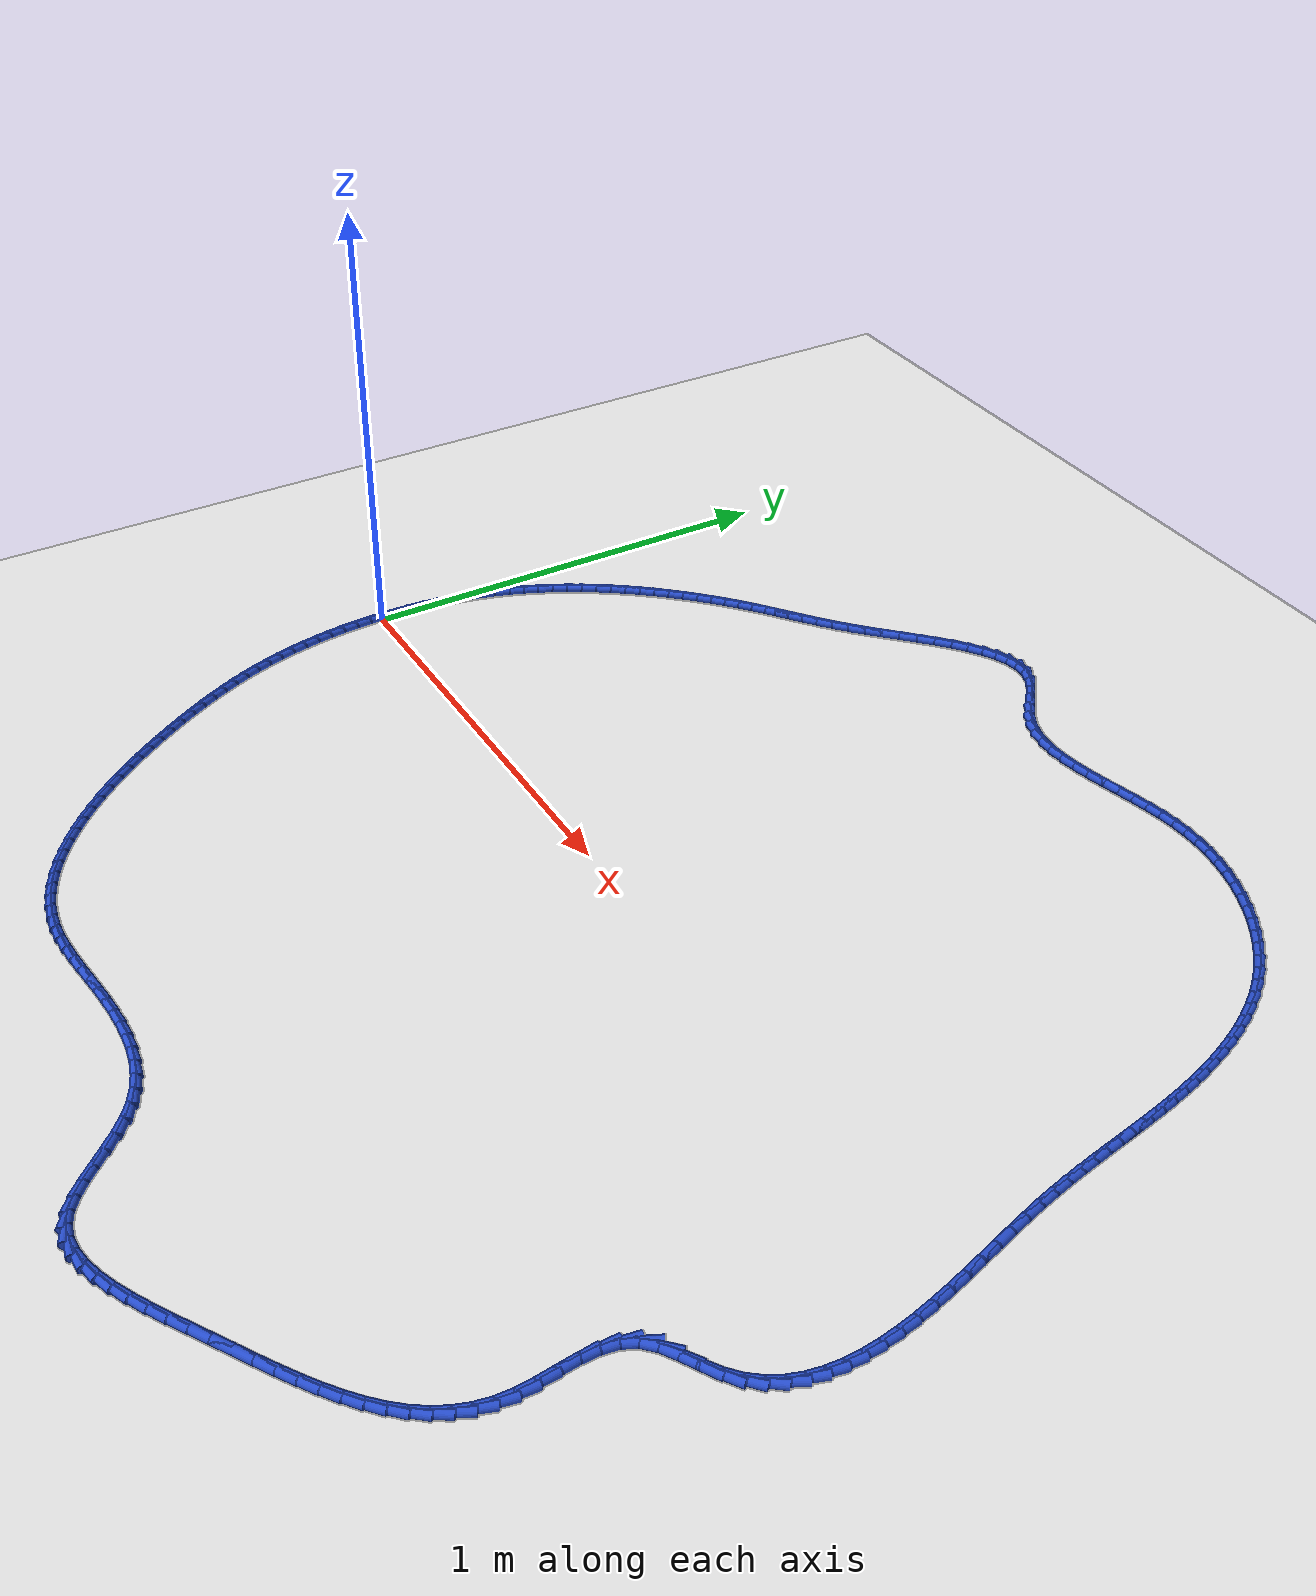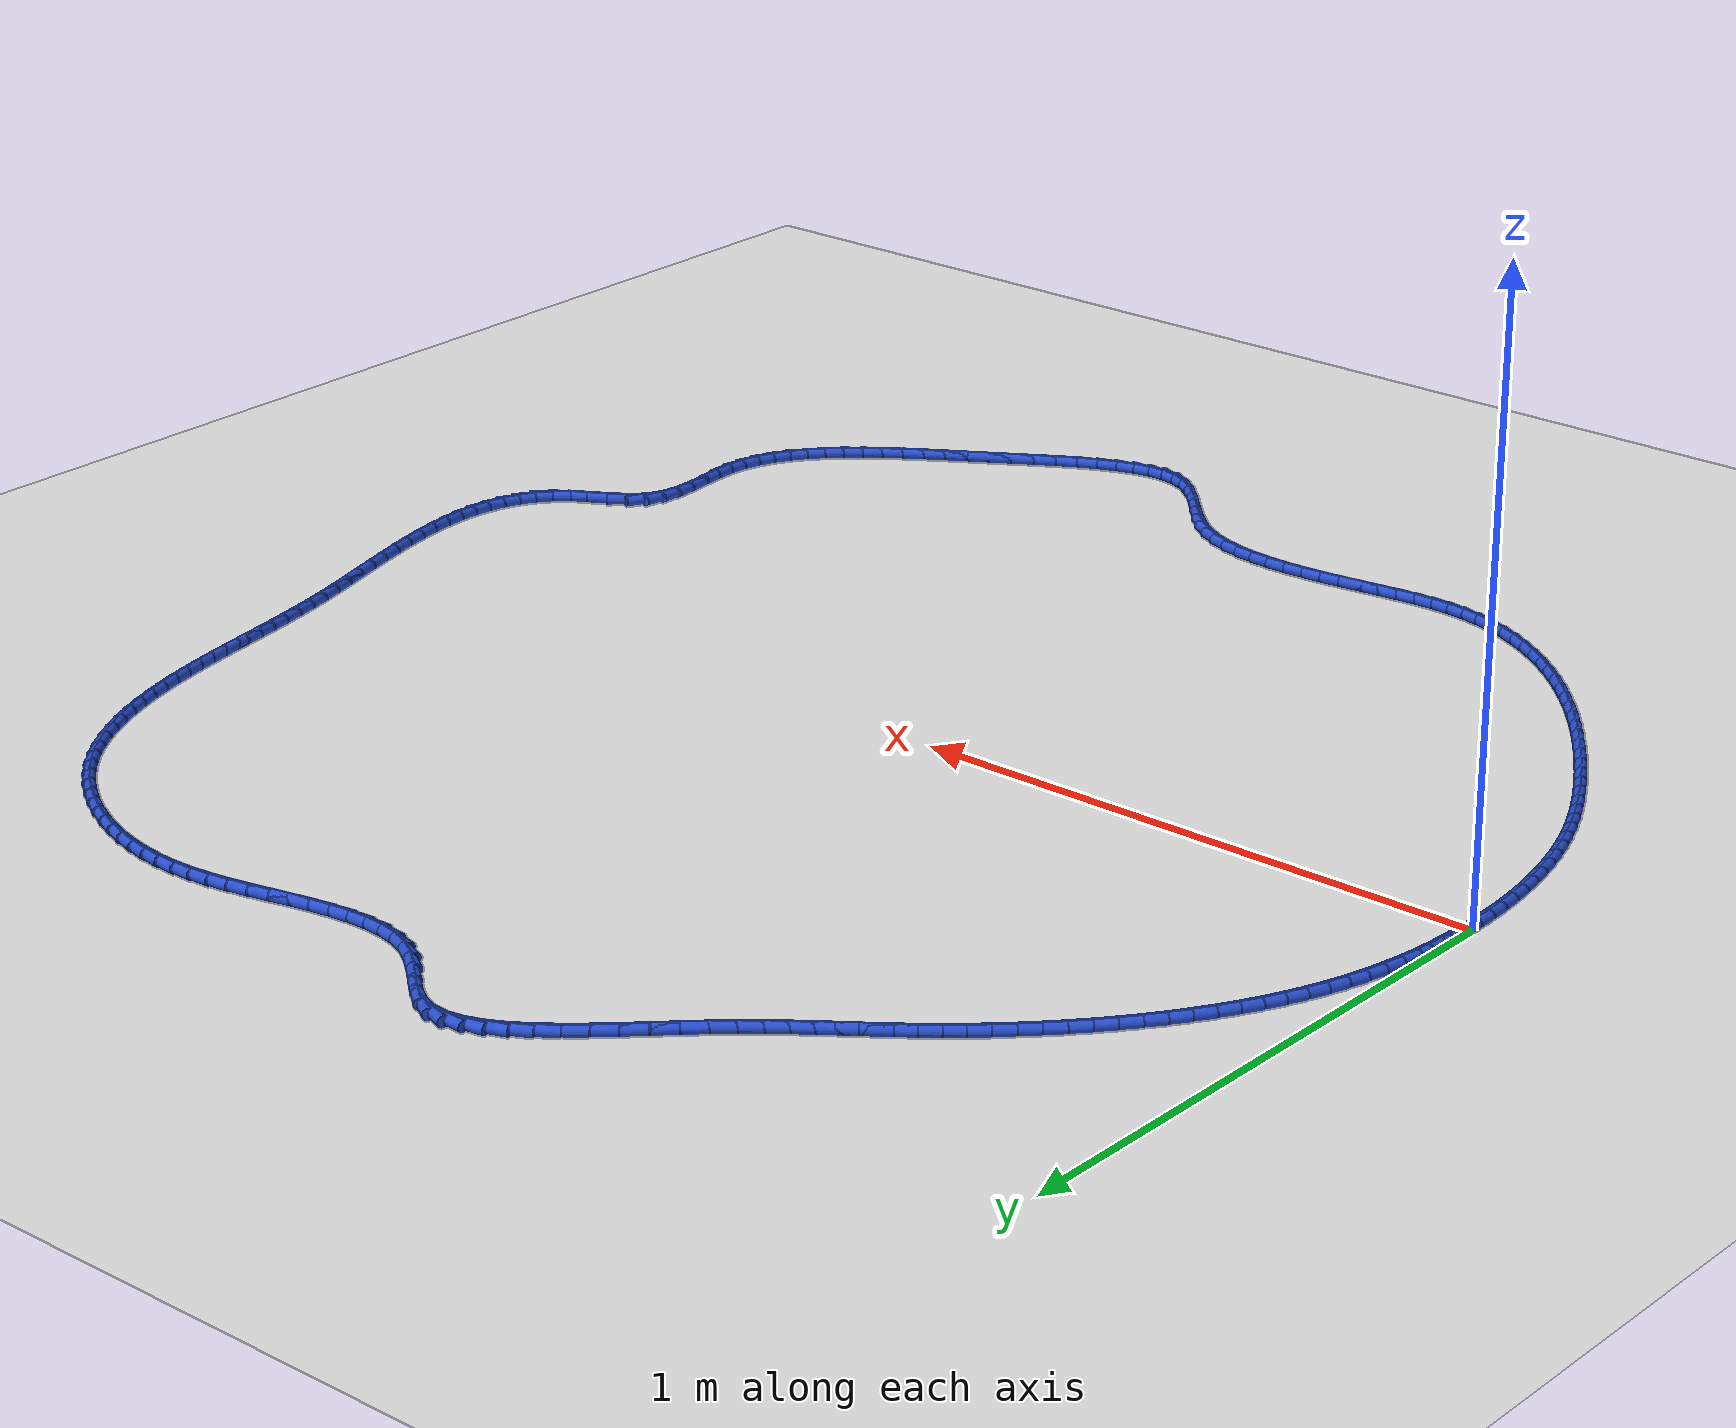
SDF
<sdf version="1.6">
 <world name="default">
  <light name="sun" type="directional">
   <pose>0 0 10 0 -0 0</pose>
   <diffuse>0.8 0.8 0.8 1</diffuse>
   <specular>0.2 0.2 0.2 1</specular>
   <attenuation>
    <range>1000</range>
    <constant>0.9</constant>
    <linear>0.01</linear>
    <quadratic>0.001</quadratic>
   </attenuation>
   <direction>-0.5 0.1 -0.9</direction>
  </light>
  <model name="ground_plane">
   <static>1</static>
   <link name="link">
    <collision name="collision">
     <geometry><plane><normal>0 0 1</normal><size>100 100</size></plane></geometry>
     <surface><friction><ode><mu>100</mu><mu2>50</mu2></ode></friction></surface>
    </collision>
    <visual name="visual">
     <cast_shadows>0</cast_shadows>
     <geometry><plane><normal>0 0 1</normal><size>100 100</size></plane></geometry>
     <material>
      <script><uri>file://media/materials/scripts/gazebo.material</uri><name>Gazebo/WhiteGlow</name></script>
     </material>
    </visual>
   </link>
  </model>
  <gravity>0 0 -9.8</gravity>
  <magnetic_field>6e-06 2.3e-05 -4.2e-05</magnetic_field>
  <atmosphere type="adiabatic"/>
  <physics name="default_physics" default="0" type="ode">
   <max_step_size>0.001</max_step_size>
   <real_time_factor>1</real_time_factor>
   <real_time_update_rate>1000</real_time_update_rate>
  </physics>
  <scene><ambient>0.4 0.4 0.4 1</ambient><background>0.7 0.7 0.7 1</background><shadows>1</shadows></scene>
  <spherical_coordinates>
   <surface_model>EARTH_WGS84</surface_model>
   <latitude_deg>0</latitude_deg>
   <longitude_deg>0</longitude_deg>
   <elevation>0</elevation>
   <heading_deg>0</heading_deg>
  </spherical_coordinates>
  <model name="line">
   <link name="link_0">
    <pose>1.9949319973733282e-17 5.551115123125783e-17 0.01 0 1.57 1.5623673042592516</pose>
    <collision name="collision">
     <geometry><cylinder><radius>0.01</radius><length>0.08</length></cylinder></geometry>
    </collision>
    <visual name="visual">
     <material>
      <script><name>Gazebo/Blue</name><uri>file://media/materials/scripts/gazebo.material</uri></script>
     </material>
     <geometry><cylinder><radius>0.01</radius><length>0.08</length></cylinder></geometry>
    </visual>
   </link>
   <link name="link_1">
    <pose>0.0002909454988560638 0.03451629262906619 0.01 0 1.57 1.5297102532509206</pose>
    <collision name="collision">
     <geometry><cylinder><radius>0.01</radius><length>0.08</length></cylinder></geometry>
    </collision>
    <visual name="visual">
     <material>
      <script><name>Gazebo/Blue</name><uri>file://media/materials/scripts/gazebo.material</uri></script>
     </material>
     <geometry><cylinder><radius>0.01</radius><length>0.08</length></cylinder></geometry>
    </visual>
   </link>
   <link name="link_2">
    <pose>0.0017065868075871354 0.0689524052087415 0.01 0 1.57 1.4953168891294837</pose>
    <collision name="collision">
     <geometry><cylinder><radius>0.01</radius><length>0.08</length></cylinder></geometry>
    </collision>
    <visual name="visual">
     <material>
      <script><name>Gazebo/Blue</name><uri>file://media/materials/scripts/gazebo.material</uri></script>
     </material>
     <geometry><cylinder><radius>0.01</radius><length>0.08</length></cylinder></geometry>
    </visual>
   </link>
   <link name="link_3">
    <pose>0.0043013560823109195 0.1032642640348845 0.01 0 1.57 1.459138099619481</pose>
    <collision name="collision">
     <geometry><cylinder><radius>0.01</radius><length>0.08</length></cylinder></geometry>
    </collision>
    <visual name="visual">
     <material>
      <script><name>Gazebo/Blue</name><uri>file://media/materials/scripts/gazebo.material</uri></script>
     </material>
     <geometry><cylinder><radius>0.01</radius><length>0.08</length></cylinder></geometry>
    </visual>
   </link>
   <link name="link_4">
    <pose>0.00812968547914511 0.1374077954033538 0.01 0 1.57 1.4211382745538208</pose>
    <collision name="collision">
     <geometry><cylinder><radius>0.01</radius><length>0.08</length></cylinder></geometry>
    </collision>
    <visual name="visual">
     <material>
      <script><name>Gazebo/Blue</name><uri>file://media/materials/scripts/gazebo.material</uri></script>
     </material>
     <geometry><cylinder><radius>0.01</radius><length>0.08</length></cylinder></geometry>
    </visual>
   </link>
   <link name="link_5">
    <pose>0.013246007154207396 0.1713389256100079 0.01 0 1.57 1.3812991831218653</pose>
    <collision name="collision">
     <geometry><cylinder><radius>0.01</radius><length>0.08</length></cylinder></geometry>
    </collision>
    <visual name="visual">
     <material>
      <script><name>Gazebo/Blue</name><uri>file://media/materials/scripts/gazebo.material</uri></script>
     </material>
     <geometry><cylinder><radius>0.01</radius><length>0.08</length></cylinder></geometry>
    </visual>
   </link>
   <link name="link_6">
    <pose>0.019704753263615468 0.2050135809507054 0.01 0 1.57 1.3396241294312707</pose>
    <collision name="collision">
     <geometry><cylinder><radius>0.01</radius><length>0.08</length></cylinder></geometry>
    </collision>
    <visual name="visual">
     <material>
      <script><name>Gazebo/Blue</name><uri>file://media/materials/scripts/gazebo.material</uri></script>
     </material>
     <geometry><cylinder><radius>0.01</radius><length>0.08</length></cylinder></geometry>
    </visual>
   </link>
   <link name="link_7">
    <pose>0.027560355963487035 0.23838768772130486 0.01 0 1.57 1.296142189354954</pose>
    <collision name="collision">
     <geometry><cylinder><radius>0.01</radius><length>0.08</length></cylinder></geometry>
    </collision>
    <visual name="visual">
     <material>
      <script><name>Gazebo/Blue</name><uri>file://media/materials/scripts/gazebo.material</uri></script>
     </material>
     <geometry><cylinder><radius>0.01</radius><length>0.08</length></cylinder></geometry>
    </visual>
   </link>
   <link name="link_8">
    <pose>0.03686724740993974 0.2714171722176647 0.01 0 1.57 1.2509273169655566</pose>
    <collision name="collision">
     <geometry><cylinder><radius>0.01</radius><length>0.08</length></cylinder></geometry>
    </collision>
    <visual name="visual">
     <material>
      <script><name>Gazebo/Blue</name><uri>file://media/materials/scripts/gazebo.material</uri></script>
     </material>
     <geometry><cylinder><radius>0.01</radius><length>0.08</length></cylinder></geometry>
    </visual>
   </link>
   <link name="link_9">
    <pose>0.047679331502748376 0.3040580137497771 0.01 0 1.57 1.2053582620434384</pose>
    <collision name="collision">
     <geometry><cylinder><radius>0.01</radius><length>0.08</length></cylinder></geometry>
    </collision>
    <visual name="visual">
     <material>
      <script><name>Gazebo/Blue</name><uri>file://media/materials/scripts/gazebo.material</uri></script>
     </material>
     <geometry><cylinder><radius>0.01</radius><length>0.08</length></cylinder></geometry>
    </visual>
   </link>
   <link name="link_10">
    <pose>0.060004717376022476 0.33627078744526323 0.01 0 1.57 1.1617174851392114</pose>
    <collision name="collision">
     <geometry><cylinder><radius>0.01</radius><length>0.08</length></cylinder></geometry>
    </collision>
    <visual name="visual">
     <material>
      <script><name>Gazebo/Blue</name><uri>file://media/materials/scripts/gazebo.material</uri></script>
     </material>
     <geometry><cylinder><radius>0.01</radius><length>0.08</length></cylinder></geometry>
    </visual>
   </link>
   <link name="link_11">
    <pose>0.07377095935128009 0.36802415265758376 0.01 0 1.57 1.1201609324612012</pose>
    <collision name="collision">
     <geometry><cylinder><radius>0.01</radius><length>0.08</length></cylinder></geometry>
    </collision>
    <visual name="visual">
     <material>
      <script><name>Gazebo/Blue</name><uri>file://media/materials/scripts/gazebo.material</uri></script>
     </material>
     <geometry><cylinder><radius>0.01</radius><length>0.08</length></cylinder></geometry>
    </visual>
   </link>
   <link name="link_12">
    <pose>0.08889742850880628 0.39928758998436864 0.01 0 1.57 1.0805907010333862</pose>
    <collision name="collision">
     <geometry><cylinder><radius>0.01</radius><length>0.08</length></cylinder></geometry>
    </collision>
    <visual name="visual">
     <material>
      <script><name>Gazebo/Blue</name><uri>file://media/materials/scripts/gazebo.material</uri></script>
     </material>
     <geometry><cylinder><radius>0.01</radius><length>0.08</length></cylinder></geometry>
    </visual>
   </link>
   <link name="link_13">
    <pose>0.10530349592888621 0.4300305800232486 0.01 0 1.57 1.0428943098141974</pose>
    <collision name="collision">
     <geometry><cylinder><radius>0.01</radius><length>0.08</length></cylinder></geometry>
    </collision>
    <visual name="visual">
     <material>
      <script><name>Gazebo/Blue</name><uri>file://media/materials/scripts/gazebo.material</uri></script>
     </material>
     <geometry><cylinder><radius>0.01</radius><length>0.08</length></cylinder></geometry>
    </visual>
   </link>
   <link name="link_14">
    <pose>0.122908532691805 0.4602226033718537 0.01 0 1.57 1.006949480206665</pose>
    <collision name="collision">
     <geometry><cylinder><radius>0.01</radius><length>0.08</length></cylinder></geometry>
    </collision>
    <visual name="visual">
     <material>
      <script><name>Gazebo/Blue</name><uri>file://media/materials/scripts/gazebo.material</uri></script>
     </material>
     <geometry><cylinder><radius>0.01</radius><length>0.08</length></cylinder></geometry>
    </visual>
   </link>
   <link name="link_15">
    <pose>0.1416319098778478 0.48983314062781436 0.01 0 1.57 0.9726278926928924</pose>
    <collision name="collision">
     <geometry><cylinder><radius>0.01</radius><length>0.08</length></cylinder></geometry>
    </collision>
    <visual name="visual">
     <material>
      <script><name>Gazebo/Blue</name><uri>file://media/materials/scripts/gazebo.material</uri></script>
     </material>
     <geometry><cylinder><radius>0.01</radius><length>0.08</length></cylinder></geometry>
    </visual>
   </link>
   <link name="link_16">
    <pose>0.16139299856729963 0.518831672388761 0.01 0 1.57 0.9397980050142196</pose>
    <collision name="collision">
     <geometry><cylinder><radius>0.01</radius><length>0.08</length></cylinder></geometry>
    </collision>
    <visual name="visual">
     <material>
      <script><name>Gazebo/Blue</name><uri>file://media/materials/scripts/gazebo.material</uri></script>
     </material>
     <geometry><cylinder><radius>0.01</radius><length>0.08</length></cylinder></geometry>
    </visual>
   </link>
   <link name="link_17">
    <pose>0.18211116984044576 0.547187679252324 0.01 0 1.57 0.9083270444999217</pose>
    <collision name="collision">
     <geometry><cylinder><radius>0.01</radius><length>0.08</length></cylinder></geometry>
    </collision>
    <visual name="visual">
     <material>
      <script><name>Gazebo/Blue</name><uri>file://media/materials/scripts/gazebo.material</uri></script>
     </material>
     <geometry><cylinder><radius>0.01</radius><length>0.08</length></cylinder></geometry>
    </visual>
   </link>
   <link name="link_18">
    <pose>0.2037057947775712 0.5748706418161335 0.01 0 1.57 0.8780822926928599</pose>
    <collision name="collision">
     <geometry><cylinder><radius>0.01</radius><length>0.08</length></cylinder></geometry>
    </collision>
    <visual name="visual">
     <material>
      <script><name>Gazebo/Blue</name><uri>file://media/materials/scripts/gazebo.material</uri></script>
     </material>
     <geometry><cylinder><radius>0.01</radius><length>0.08</length></cylinder></geometry>
    </visual>
   </link>
   <link name="link_19">
    <pose>0.22609624445896115 0.6018500406778199 0.01 0 1.57 0.8489317722083948</pose>
    <collision name="collision">
     <geometry><cylinder><radius>0.01</radius><length>0.08</length></cylinder></geometry>
    </collision>
    <visual name="visual">
     <material>
      <script><name>Gazebo/Blue</name><uri>file://media/materials/scripts/gazebo.material</uri></script>
     </material>
     <geometry><cylinder><radius>0.01</radius><length>0.08</length></cylinder></geometry>
    </visual>
   </link>
   <link name="link_20">
    <pose>0.24920188996490072 0.6280953564350139 0.01 0 1.57 0.8207444296304203</pose>
    <collision name="collision">
     <geometry><cylinder><radius>0.01</radius><length>0.08</length></cylinder></geometry>
    </collision>
    <visual name="visual">
     <material>
      <script><name>Gazebo/Blue</name><uri>file://media/materials/scripts/gazebo.material</uri></script>
     </material>
     <geometry><cylinder><radius>0.01</radius><length>0.08</length></cylinder></geometry>
    </visual>
   </link>
   <link name="link_21">
    <pose>0.27294210237567496 0.6535760696853454 0.01 0 1.57 0.7933898880945509</pose>
    <collision name="collision">
     <geometry><cylinder><radius>0.01</radius><length>0.08</length></cylinder></geometry>
    </collision>
    <visual name="visual">
     <material>
      <script><name>Gazebo/Blue</name><uri>file://media/materials/scripts/gazebo.material</uri></script>
     </material>
     <geometry><cylinder><radius>0.01</radius><length>0.08</length></cylinder></geometry>
    </visual>
   </link>
   <link name="link_22">
    <pose>0.2972362527715693 0.6782616610264454 0.01 0 1.57 0.7667378213242816</pose>
    <collision name="collision">
     <geometry><cylinder><radius>0.01</radius><length>0.08</length></cylinder></geometry>
    </collision>
    <visual name="visual">
     <material>
      <script><name>Gazebo/Blue</name><uri>file://media/materials/scripts/gazebo.material</uri></script>
     </material>
     <geometry><cylinder><radius>0.01</radius><length>0.08</length></cylinder></geometry>
    </visual>
   </link>
   <link name="link_23">
    <pose>0.3220037122328683 0.7021216110559433 0.01 0 1.57 0.7406569783261147</pose>
    <collision name="collision">
     <geometry><cylinder><radius>0.01</radius><length>0.08</length></cylinder></geometry>
    </collision>
    <visual name="visual">
     <material>
      <script><name>Gazebo/Blue</name><uri>file://media/materials/scripts/gazebo.material</uri></script>
     </material>
     <geometry><cylinder><radius>0.01</radius><length>0.08</length></cylinder></geometry>
    </visual>
   </link>
   <link name="link_24">
    <pose>0.34716385183985754 0.7251254003714702 0.01 0 1.57 0.7150138648418488</pose>
    <collision name="collision">
     <geometry><cylinder><radius>0.01</radius><length>0.08</length></cylinder></geometry>
    </collision>
    <visual name="visual">
     <material>
      <script><name>Gazebo/Blue</name><uri>file://media/materials/scripts/gazebo.material</uri></script>
     </material>
     <geometry><cylinder><radius>0.01</radius><length>0.08</length></cylinder></geometry>
    </visual>
   </link>
   <link name="link_25">
    <pose>0.3726360426728219 0.7472425095706559 0.01 0 1.57 0.6896710749119628</pose>
    <collision name="collision">
     <geometry><cylinder><radius>0.01</radius><length>0.08</length></cylinder></geometry>
    </collision>
    <visual name="visual">
     <material>
      <script><name>Gazebo/Blue</name><uri>file://media/materials/scripts/gazebo.material</uri></script>
     </material>
     <geometry><cylinder><radius>0.01</radius><length>0.08</length></cylinder></geometry>
    </visual>
   </link>
   <link name="link_26">
    <pose>0.39833965599784876 0.7684424199007063 0.01 0 1.57 0.6659969141898564</pose>
    <collision name="collision">
     <geometry><cylinder><radius>0.01</radius><length>0.08</length></cylinder></geometry>
    </collision>
    <visual name="visual">
     <material>
      <script><name>Gazebo/Blue</name><uri>file://media/materials/scripts/gazebo.material</uri></script>
     </material>
     <geometry><cylinder><radius>0.01</radius><length>0.08</length></cylinder></geometry>
    </visual>
   </link>
   <link name="link_27">
    <pose>0.424217360001756 0.7887760600070499 0.01 0 1.57 0.649927666042742</pose>
    <collision name="collision">
     <geometry><cylinder><radius>0.01</radius><length>0.08</length></cylinder></geometry>
    </collision>
    <visual name="visual">
     <material>
      <script><name>Gazebo/Blue</name><uri>file://media/materials/scripts/gazebo.material</uri></script>
     </material>
     <geometry><cylinder><radius>0.01</radius><length>0.08</length></cylinder></geometry>
    </visual>
   </link>
   <link name="link_28">
    <pose>0.4502994846137048 0.8086008291163638 0.01 0 1.57 0.6433127780839777</pose>
    <collision name="collision">
     <geometry><cylinder><radius>0.01</radius><length>0.08</length></cylinder></geometry>
    </collision>
    <visual name="visual">
     <material>
      <script><name>Gazebo/Blue</name><uri>file://media/materials/scripts/gazebo.material</uri></script>
     </material>
     <geometry><cylinder><radius>0.01</radius><length>0.08</length></cylinder></geometry>
    </visual>
   </link>
   <link name="link_29">
    <pose>0.4766369747168943 0.8283461975410411 0.01 0 1.57 0.6462000515691043</pose>
    <collision name="collision">
     <geometry><cylinder><radius>0.01</radius><length>0.08</length></cylinder></geometry>
    </collision>
    <visual name="visual">
     <material>
      <script><name>Gazebo/Blue</name><uri>file://media/materials/scripts/gazebo.material</uri></script>
     </material>
     <geometry><cylinder><radius>0.01</radius><length>0.08</length></cylinder></geometry>
    </visual>
   </link>
   <link name="link_30">
    <pose>0.5032807751945245 0.8484416355934762 0.01 0 1.57 0.6581326444454488</pose>
    <collision name="collision">
     <geometry><cylinder><radius>0.01</radius><length>0.08</length></cylinder></geometry>
    </collision>
    <visual name="visual">
     <material>
      <script><name>Gazebo/Blue</name><uri>file://media/materials/scripts/gazebo.material</uri></script>
     </material>
     <geometry><cylinder><radius>0.01</radius><length>0.08</length></cylinder></geometry>
    </visual>
   </link>
   <link name="link_31">
    <pose>0.5302818309297943 0.8693166135860619 0.01 0 1.57 0.6782146613536185</pose>
    <collision name="collision">
     <geometry><cylinder><radius>0.01</radius><length>0.08</length></cylinder></geometry>
    </collision>
    <visual name="visual">
     <material>
      <script><name>Gazebo/Blue</name><uri>file://media/materials/scripts/gazebo.material</uri></script>
     </material>
     <geometry><cylinder><radius>0.01</radius><length>0.08</length></cylinder></geometry>
    </visual>
   </link>
   <link name="link_32">
    <pose>0.5576910868059037 0.8914006018311927 0.01 0 1.57 0.7052087478321921</pose>
    <collision name="collision">
     <geometry><cylinder><radius>0.01</radius><length>0.08</length></cylinder></geometry>
    </collision>
    <visual name="visual">
     <material>
      <script><name>Gazebo/Blue</name><uri>file://media/materials/scripts/gazebo.material</uri></script>
     </material>
     <geometry><cylinder><radius>0.01</radius><length>0.08</length></cylinder></geometry>
    </visual>
   </link>
   <link name="link_33">
    <pose>0.585559487706052 0.915123070641262 0.01 0 1.57 0.7370793029173643</pose>
    <collision name="collision">
     <geometry><cylinder><radius>0.01</radius><length>0.08</length></cylinder></geometry>
    </collision>
    <visual name="visual">
     <material>
      <script><name>Gazebo/Blue</name><uri>file://media/materials/scripts/gazebo.material</uri></script>
     </material>
     <geometry><cylinder><radius>0.01</radius><length>0.08</length></cylinder></geometry>
    </visual>
   </link>
   <link name="link_34">
    <pose>0.6139341287341711 0.9408800938903489 0.01 0 1.57 0.7620539981247093</pose>
    <collision name="collision">
     <geometry><cylinder><radius>0.01</radius><length>0.08</length></cylinder></geometry>
    </collision>
    <visual name="visual">
     <material>
      <script><name>Gazebo/Blue</name><uri>file://media/materials/scripts/gazebo.material</uri></script>
     </material>
     <geometry><cylinder><radius>0.01</radius><length>0.08</length></cylinder></geometry>
    </visual>
   </link>
   <link name="link_35">
    <pose>0.642787019568394 0.9684163871234431 0.01 0 1.57 0.7721066443820065</pose>
    <collision name="collision">
     <geometry><cylinder><radius>0.01</radius><length>0.08</length></cylinder></geometry>
    </collision>
    <visual name="visual">
     <material>
      <script><name>Gazebo/Blue</name><uri>file://media/materials/scripts/gazebo.material</uri></script>
     </material>
     <geometry><cylinder><radius>0.01</radius><length>0.08</length></cylinder></geometry>
    </visual>
   </link>
   <link name="link_36">
    <pose>0.6720218783697505 0.9968842440140743 0.01 0 1.57 0.7683808546019988</pose>
    <collision name="collision">
     <geometry><cylinder><radius>0.01</radius><length>0.08</length></cylinder></geometry>
    </collision>
    <visual name="visual">
     <material>
      <script><name>Gazebo/Blue</name><uri>file://media/materials/scripts/gazebo.material</uri></script>
     </material>
     <geometry><cylinder><radius>0.01</radius><length>0.08</length></cylinder></geometry>
    </visual>
   </link>
   <link name="link_37">
    <pose>0.7015399361342318 1.0254143823354347 0.01 0 1.57 0.750943738321753</pose>
    <collision name="collision">
     <geometry><cylinder><radius>0.01</radius><length>0.08</length></cylinder></geometry>
    </collision>
    <visual name="visual">
     <material>
      <script><name>Gazebo/Blue</name><uri>file://media/materials/scripts/gazebo.material</uri></script>
     </material>
     <geometry><cylinder><radius>0.01</radius><length>0.08</length></cylinder></geometry>
    </visual>
   </link>
   <link name="link_38">
    <pose>0.7312424238578288 1.053137519860716 0.01 0 1.57 0.7184919266017787</pose>
    <collision name="collision">
     <geometry><cylinder><radius>0.01</radius><length>0.08</length></cylinder></geometry>
    </collision>
    <visual name="visual">
     <material>
      <script><name>Gazebo/Blue</name><uri>file://media/materials/scripts/gazebo.material</uri></script>
     </material>
     <geometry><cylinder><radius>0.01</radius><length>0.08</length></cylinder></geometry>
    </visual>
   </link>
   <link name="link_39">
    <pose>0.761030572536532 1.0791843743631104 0.01 0 1.57 0.6681793026490517</pose>
    <collision name="collision">
     <geometry><cylinder><radius>0.01</radius><length>0.08</length></cylinder></geometry>
    </collision>
    <visual name="visual">
     <material>
      <script><name>Gazebo/Blue</name><uri>file://media/materials/scripts/gazebo.material</uri></script>
     </material>
     <geometry><cylinder><radius>0.01</radius><length>0.08</length></cylinder></geometry>
    </visual>
   </link>
   <link name="link_40">
    <pose>0.790805613166333 1.1026856636158104 0.01 0 1.57 0.5952259296368746</pose>
    <collision name="collision">
     <geometry><cylinder><radius>0.01</radius><length>0.08</length></cylinder></geometry>
    </collision>
    <visual name="visual">
     <material>
      <script><name>Gazebo/Blue</name><uri>file://media/materials/scripts/gazebo.material</uri></script>
     </material>
     <geometry><cylinder><radius>0.01</radius><length>0.08</length></cylinder></geometry>
    </visual>
   </link>
   <link name="link_41">
    <pose>0.8204687767432229 1.1227721053920081 0.01 0 1.57 0.4924468060649312</pose>
    <collision name="collision">
     <geometry><cylinder><radius>0.01</radius><length>0.08</length></cylinder></geometry>
    </collision>
    <visual name="visual">
     <material>
      <script><name>Gazebo/Blue</name><uri>file://media/materials/scripts/gazebo.material</uri></script>
     </material>
     <geometry><cylinder><radius>0.01</radius><length>0.08</length></cylinder></geometry>
    </visual>
   </link>
   <link name="link_42">
    <pose>0.8499212942631922 1.1385744174648946 0.01 0 1.57 0.3503281027424072</pose>
    <collision name="collision">
     <geometry><cylinder><radius>0.01</radius><length>0.08</length></cylinder></geometry>
    </collision>
    <visual name="visual">
     <material>
      <script><name>Gazebo/Blue</name><uri>file://media/materials/scripts/gazebo.material</uri></script>
     </material>
     <geometry><cylinder><radius>0.01</radius><length>0.08</length></cylinder></geometry>
    </visual>
   </link>
   <link name="link_43">
    <pose>0.8790643967222324 1.1492233176076632 0.01 0 1.57 0.15962621810410652</pose>
    <collision name="collision">
     <geometry><cylinder><radius>0.01</radius><length>0.08</length></cylinder></geometry>
    </collision>
    <visual name="visual">
     <material>
      <script><name>Gazebo/Blue</name><uri>file://media/materials/scripts/gazebo.material</uri></script>
     </material>
     <geometry><cylinder><radius>0.01</radius><length>0.08</length></cylinder></geometry>
    </visual>
   </link>
   <link name="link_44">
    <pose>0.9077993151163342 1.1538495235935051 0.01 0 1.57 -0.08009515208632245</pose>
    <collision name="collision">
     <geometry><cylinder><radius>0.01</radius><length>0.08</length></cylinder></geometry>
    </collision>
    <visual name="visual">
     <material>
      <script><name>Gazebo/Blue</name><uri>file://media/materials/scripts/gazebo.material</uri></script>
     </material>
     <geometry><cylinder><radius>0.01</radius><length>0.08</length></cylinder></geometry>
    </visual>
   </link>
   <link name="link_45">
    <pose>0.9360272804414886 1.1515837531956135 0.01 0 1.57 -0.34758033462060545</pose>
    <collision name="collision">
     <geometry><cylinder><radius>0.01</radius><length>0.08</length></cylinder></geometry>
    </collision>
    <visual name="visual">
     <material>
      <script><name>Gazebo/Blue</name><uri>file://media/materials/scripts/gazebo.material</uri></script>
     </material>
     <geometry><cylinder><radius>0.01</radius><length>0.08</length></cylinder></geometry>
    </visual>
   </link>
   <link name="link_46">
    <pose>0.9636521820846191 1.1415755597997055 0.01 0 1.57 -0.5663463048453913</pose>
    <collision name="collision">
     <geometry><cylinder><radius>0.01</radius><length>0.08</length></cylinder></geometry>
    </collision>
    <visual name="visual">
     <material>
      <script><name>Gazebo/Blue</name><uri>file://media/materials/scripts/gazebo.material</uri></script>
     </material>
     <geometry><cylinder><radius>0.01</radius><length>0.08</length></cylinder></geometry>
    </visual>
   </link>
   <link name="link_47">
    <pose>0.9907697186125279 1.1243335306894484 0.01 0 1.57 -0.6769637941260811</pose>
    <collision name="collision">
     <geometry><cylinder><radius>0.01</radius><length>0.08</length></cylinder></geometry>
    </collision>
    <visual name="visual">
     <material>
      <script><name>Gazebo/Blue</name><uri>file://media/materials/scripts/gazebo.material</uri></script>
     </material>
     <geometry><cylinder><radius>0.01</radius><length>0.08</length></cylinder></geometry>
    </visual>
   </link>
   <link name="link_48">
    <pose>1.017793126151487 1.1026161157852472 0.01 0 1.57 -0.7035716356010284</pose>
    <collision name="collision">
     <geometry><cylinder><radius>0.01</radius><length>0.08</length></cylinder></geometry>
    </collision>
    <visual name="visual">
     <material>
      <script><name>Gazebo/Blue</name><uri>file://media/materials/scripts/gazebo.material</uri></script>
     </material>
     <geometry><cylinder><radius>0.01</radius><length>0.08</length></cylinder></geometry>
    </visual>
   </link>
   <link name="link_49">
    <pose>1.0451654657118885 1.0793930845519915 0.01 0 1.57 -0.657789227405496</pose>
    <collision name="collision">
     <geometry><cylinder><radius>0.01</radius><length>0.08</length></cylinder></geometry>
    </collision>
    <visual name="visual">
     <material>
      <script><name>Gazebo/Blue</name><uri>file://media/materials/scripts/gazebo.material</uri></script>
     </material>
     <geometry><cylinder><radius>0.01</radius><length>0.08</length></cylinder></geometry>
    </visual>
   </link>
   <link name="link_50">
    <pose>1.0733297983041235 1.057634206454571 0.01 0 1.57 -0.5340474500768945</pose>
    <collision name="collision">
     <geometry><cylinder><radius>0.01</radius><length>0.08</length></cylinder></geometry>
    </collision>
    <visual name="visual">
     <material>
      <script><name>Gazebo/Blue</name><uri>file://media/materials/scripts/gazebo.material</uri></script>
     </material>
     <geometry><cylinder><radius>0.01</radius><length>0.08</length></cylinder></geometry>
    </visual>
   </link>
   <link name="link_51">
    <pose>1.102719932568063 1.0402538538285762 0.01 0 1.57 -0.3642983789219908</pose>
    <collision name="collision">
     <geometry><cylinder><radius>0.01</radius><length>0.08</length></cylinder></geometry>
    </collision>
    <visual name="visual">
     <material>
      <script><name>Gazebo/Blue</name><uri>file://media/materials/scripts/gazebo.material</uri></script>
     </material>
     <geometry><cylinder><radius>0.01</radius><length>0.08</length></cylinder></geometry>
    </visual>
   </link>
   <link name="link_52">
    <pose>1.1334945207863705 1.0285189431209687 0.01 0 1.57 -0.20663789408005165</pose>
    <collision name="collision">
     <geometry><cylinder><radius>0.01</radius><length>0.08</length></cylinder></geometry>
    </collision>
    <visual name="visual">
     <material>
      <script><name>Gazebo/Blue</name><uri>file://media/materials/scripts/gazebo.material</uri></script>
     </material>
     <geometry><cylinder><radius>0.01</radius><length>0.08</length></cylinder></geometry>
    </visual>
   </link>
   <link name="link_53">
    <pose>1.1654971890544448 1.021810220484296 0.01 0 1.57 -0.07263104191738969</pose>
    <collision name="collision">
     <geometry><cylinder><radius>0.01</radius><length>0.08</length></cylinder></geometry>
    </collision>
    <visual name="visual">
     <material>
      <script><name>Gazebo/Blue</name><uri>file://media/materials/scripts/gazebo.material</uri></script>
     </material>
     <geometry><cylinder><radius>0.01</radius><length>0.08</length></cylinder></geometry>
    </visual>
   </link>
   <link name="link_54">
    <pose>1.198554291333085 1.0194050178518521 0.01 0 1.57 0.034627355146794686</pose>
    <collision name="collision">
     <geometry><cylinder><radius>0.01</radius><length>0.08</length></cylinder></geometry>
    </collision>
    <visual name="visual">
     <material>
      <script><name>Gazebo/Blue</name><uri>file://media/materials/scripts/gazebo.material</uri></script>
     </material>
     <geometry><cylinder><radius>0.01</radius><length>0.08</length></cylinder></geometry>
    </visual>
   </link>
   <link name="link_55">
    <pose>1.2324921815830912 1.0205806671569304 0.01 0 1.57 0.11591132369253221</pose>
    <collision name="collision">
     <geometry><cylinder><radius>0.01</radius><length>0.08</length></cylinder></geometry>
    </collision>
    <visual name="visual">
     <material>
      <script><name>Gazebo/Blue</name><uri>file://media/materials/scripts/gazebo.material</uri></script>
     </material>
     <geometry><cylinder><radius>0.01</radius><length>0.08</length></cylinder></geometry>
    </visual>
   </link>
   <link name="link_56">
    <pose>1.2671372137652637 1.0246145003328253 0.01 0 1.57 0.17360714549006903</pose>
    <collision name="collision">
     <geometry><cylinder><radius>0.01</radius><length>0.08</length></cylinder></geometry>
    </collision>
    <visual name="visual">
     <material>
      <script><name>Gazebo/Blue</name><uri>file://media/materials/scripts/gazebo.material</uri></script>
     </material>
     <geometry><cylinder><radius>0.01</radius><length>0.08</length></cylinder></geometry>
    </visual>
   </link>
   <link name="link_57">
    <pose>1.302315741840401 1.0307838493128298 0.01 0 1.57 0.21020078275851078</pose>
    <collision name="collision">
     <geometry><cylinder><radius>0.01</radius><length>0.08</length></cylinder></geometry>
    </collision>
    <visual name="visual">
     <material>
      <script><name>Gazebo/Blue</name><uri>file://media/materials/scripts/gazebo.material</uri></script>
     </material>
     <geometry><cylinder><radius>0.01</radius><length>0.08</length></cylinder></geometry>
    </visual>
   </link>
   <link name="link_58">
    <pose>1.337854119769304 1.0383660460302393 0.01 0 1.57 0.2275492981983495</pose>
    <collision name="collision">
     <geometry><cylinder><radius>0.01</radius><length>0.08</length></cylinder></geometry>
    </collision>
    <visual name="visual">
     <material>
      <script><name>Gazebo/Blue</name><uri>file://media/materials/scripts/gazebo.material</uri></script>
     </material>
     <geometry><cylinder><radius>0.01</radius><length>0.08</length></cylinder></geometry>
    </visual>
   </link>
   <link name="link_59">
    <pose>1.373578701512772 1.046638422418346 0.01 0 1.57 0.22660903773751515</pose>
    <collision name="collision">
     <geometry><cylinder><radius>0.01</radius><length>0.08</length></cylinder></geometry>
    </collision>
    <visual name="visual">
     <material>
      <script><name>Gazebo/Blue</name><uri>file://media/materials/scripts/gazebo.material</uri></script>
     </material>
     <geometry><cylinder><radius>0.01</radius><length>0.08</length></cylinder></geometry>
    </visual>
   </link>
   <link name="link_60">
    <pose>1.4093158410316056 1.054878310410445 0.01 0 1.57 0.2073626266164129</pose>
    <collision name="collision">
     <geometry><cylinder><radius>0.01</radius><length>0.08</length></cylinder></geometry>
    </collision>
    <visual name="visual">
     <material>
      <script><name>Gazebo/Blue</name><uri>file://media/materials/scripts/gazebo.material</uri></script>
     </material>
     <geometry><cylinder><radius>0.01</radius><length>0.08</length></cylinder></geometry>
    </visual>
   </link>
   <link name="link_61">
    <pose>1.4448918922866034 1.0623630419398298 0.01 0 1.57 0.16882816117359226</pose>
    <collision name="collision">
     <geometry><cylinder><radius>0.01</radius><length>0.08</length></cylinder></geometry>
    </collision>
    <visual name="visual">
     <material>
      <script><name>Gazebo/Blue</name><uri>file://media/materials/scripts/gazebo.material</uri></script>
     </material>
     <geometry><cylinder><radius>0.01</radius><length>0.08</length></cylinder></geometry>
    </visual>
   </link>
   <link name="link_62">
    <pose>1.4801332092385664 1.0683699489397944 0.01 0 1.57 0.11010865503921563</pose>
    <collision name="collision">
     <geometry><cylinder><radius>0.01</radius><length>0.08</length></cylinder></geometry>
    </collision>
    <visual name="visual">
     <material>
      <script><name>Gazebo/Blue</name><uri>file://media/materials/scripts/gazebo.material</uri></script>
     </material>
     <geometry><cylinder><radius>0.01</radius><length>0.08</length></cylinder></geometry>
    </visual>
   </link>
   <link name="link_63">
    <pose>1.5148835955431212 1.0722118059185342 0.01 0 1.57 0.04048648177134366</pose>
    <collision name="collision">
     <geometry><cylinder><radius>0.01</radius><length>0.08</length></cylinder></geometry>
    </collision>
    <visual name="visual">
     <material>
      <script><name>Gazebo/Blue</name><uri>file://media/materials/scripts/gazebo.material</uri></script>
     </material>
     <geometry><cylinder><radius>0.01</radius><length>0.08</length></cylinder></geometry>
    </visual>
   </link>
   <link name="link_64">
    <pose>1.5491837253871417 1.0736012567583848 0.01 0 1.57 -0.032268470238282845</pose>
    <collision name="collision">
     <geometry><cylinder><radius>0.01</radius><length>0.08</length></cylinder></geometry>
    </collision>
    <visual name="visual">
     <material>
      <script><name>Gazebo/Blue</name><uri>file://media/materials/scripts/gazebo.material</uri></script>
     </material>
     <geometry><cylinder><radius>0.01</radius><length>0.08</length></cylinder></geometry>
    </visual>
   </link>
   <link name="link_65">
    <pose>1.583198502156696 1.0725032708259334 0.01 0 1.57 -0.10627540384655525</pose>
    <collision name="collision">
     <geometry><cylinder><radius>0.01</radius><length>0.08</length></cylinder></geometry>
    </collision>
    <visual name="visual">
     <material>
      <script><name>Gazebo/Blue</name><uri>file://media/materials/scripts/gazebo.material</uri></script>
     </material>
     <geometry><cylinder><radius>0.01</radius><length>0.08</length></cylinder></geometry>
    </visual>
   </link>
   <link name="link_66">
    <pose>1.6170926354868682 1.0688875352620786 0.01 0 1.57 -0.17902174745376503</pose>
    <collision name="collision">
     <geometry><cylinder><radius>0.01</radius><length>0.08</length></cylinder></geometry>
    </collision>
    <visual name="visual">
     <material>
      <script><name>Gazebo/Blue</name><uri>file://media/materials/scripts/gazebo.material</uri></script>
     </material>
     <geometry><cylinder><radius>0.01</radius><length>0.08</length></cylinder></geometry>
    </visual>
   </link>
   <link name="link_67">
    <pose>1.6509018016746273 1.0627694602191808 0.01 0 1.57 -0.24901686770144857</pose>
    <collision name="collision">
     <geometry><cylinder><radius>0.01</radius><length>0.08</length></cylinder></geometry>
    </collision>
    <visual name="visual">
     <material>
      <script><name>Gazebo/Blue</name><uri>file://media/materials/scripts/gazebo.material</uri></script>
     </material>
     <geometry><cylinder><radius>0.01</radius><length>0.08</length></cylinder></geometry>
    </visual>
   </link>
   <link name="link_68">
    <pose>1.6844614030042033 1.0542354230206774 0.01 0 1.57 -0.3167102250577751</pose>
    <collision name="collision">
     <geometry><cylinder><radius>0.01</radius><length>0.08</length></cylinder></geometry>
    </collision>
    <visual name="visual">
     <material>
      <script><name>Gazebo/Blue</name><uri>file://media/materials/scripts/gazebo.material</uri></script>
     </material>
     <geometry><cylinder><radius>0.01</radius><length>0.08</length></cylinder></geometry>
    </visual>
   </link>
   <link name="link_69">
    <pose>1.717589582018257 1.0433779169858637 0.01 0 1.57 -0.38269236614280666</pose>
    <collision name="collision">
     <geometry><cylinder><radius>0.01</radius><length>0.08</length></cylinder></geometry>
    </collision>
    <visual name="visual">
     <material>
      <script><name>Gazebo/Blue</name><uri>file://media/materials/scripts/gazebo.material</uri></script>
     </material>
     <geometry><cylinder><radius>0.01</radius><length>0.08</length></cylinder></geometry>
    </visual>
   </link>
   <link name="link_70">
    <pose>1.7501044812594508 1.030289435434035 0.01 0 1.57 -0.4475578443174234</pose>
    <collision name="collision">
     <geometry><cylinder><radius>0.01</radius><length>0.08</length></cylinder></geometry>
    </collision>
    <visual name="visual">
     <material>
      <script><name>Gazebo/Blue</name><uri>file://media/materials/scripts/gazebo.material</uri></script>
     </material>
     <geometry><cylinder><radius>0.01</radius><length>0.08</length></cylinder></geometry>
    </visual>
   </link>
   <link name="link_71">
    <pose>1.7818242432704472 1.0150624716844867 0.01 0 1.57 -0.5118987391741399</pose>
    <collision name="collision">
     <geometry><cylinder><radius>0.01</radius><length>0.08</length></cylinder></geometry>
    </collision>
    <visual name="visual">
     <material>
      <script><name>Gazebo/Blue</name><uri>file://media/materials/scripts/gazebo.material</uri></script>
     </material>
     <geometry><cylinder><radius>0.01</radius><length>0.08</length></cylinder></geometry>
    </visual>
   </link>
   <link name="link_72">
    <pose>1.812567010593908 0.9977895190565139 0.01 0 1.57 -0.5763016322463971</pose>
    <collision name="collision">
     <geometry><cylinder><radius>0.01</radius><length>0.08</length></cylinder></geometry>
    </collision>
    <visual name="visual">
     <material>
      <script><name>Gazebo/Blue</name><uri>file://media/materials/scripts/gazebo.material</uri></script>
     </material>
     <geometry><cylinder><radius>0.01</radius><length>0.08</length></cylinder></geometry>
    </visual>
   </link>
   <link name="link_73">
    <pose>1.8421509257724957 0.9785630708694116 0.01 0 1.57 -0.6413459519899606</pose>
    <collision name="collision">
     <geometry><cylinder><radius>0.01</radius><length>0.08</length></cylinder></geometry>
    </collision>
    <visual name="visual">
     <material>
      <script><name>Gazebo/Blue</name><uri>file://media/materials/scripts/gazebo.material</uri></script>
     </material>
     <geometry><cylinder><radius>0.01</radius><length>0.08</length></cylinder></geometry>
    </visual>
   </link>
   <link name="link_74">
    <pose>1.8703941313488714 0.9574756204424754 0.01 0 1.57 -0.7076017939944604</pose>
    <collision name="collision">
     <geometry><cylinder><radius>0.01</radius><length>0.08</length></cylinder></geometry>
    </collision>
    <visual name="visual">
     <material>
      <script><name>Gazebo/Blue</name><uri>file://media/materials/scripts/gazebo.material</uri></script>
     </material>
     <geometry><cylinder><radius>0.01</radius><length>0.08</length></cylinder></geometry>
    </visual>
   </link>
   <link name="link_75">
    <pose>1.8971147698656987 0.9346196610950009 0.01 0 1.57 -0.7756253816816602</pose>
    <collision name="collision">
     <geometry><cylinder><radius>0.01</radius><length>0.08</length></cylinder></geometry>
    </collision>
    <visual name="visual">
     <material>
      <script><name>Gazebo/Blue</name><uri>file://media/materials/scripts/gazebo.material</uri></script>
     </material>
     <geometry><cylinder><radius>0.01</radius><length>0.08</length></cylinder></geometry>
    </visual>
   </link>
   <link name="link_76">
    <pose>1.9221309838656389 0.9100876861462822 0.01 0 1.57 -0.8459326086933203</pose>
    <collision name="collision">
     <geometry><cylinder><radius>0.01</radius><length>0.08</length></cylinder></geometry>
    </collision>
    <visual name="visual">
     <material>
      <script><name>Gazebo/Blue</name><uri>file://media/materials/scripts/gazebo.material</uri></script>
     </material>
     <geometry><cylinder><radius>0.01</radius><length>0.08</length></cylinder></geometry>
    </visual>
   </link>
   <link name="link_77">
    <pose>1.9452615540875606 0.8839723985985112 0.01 0 1.57 -0.9164689290670467</pose>
    <collision name="collision">
     <geometry><cylinder><radius>0.01</radius><length>0.08</length></cylinder></geometry>
    </collision>
    <visual name="visual">
     <material>
      <script><name>Gazebo/Blue</name><uri>file://media/materials/scripts/gazebo.material</uri></script>
     </material>
     <geometry><cylinder><radius>0.01</radius><length>0.08</length></cylinder></geometry>
    </visual>
   </link>
   <link name="link_78">
    <pose>1.9664143496878275 0.8563957719464457 0.01 0 1.57 -0.9822001873342894</pose>
    <collision name="collision">
     <geometry><cylinder><radius>0.01</radius><length>0.08</length></cylinder></geometry>
    </collision>
    <visual name="visual">
     <material>
      <script><name>Gazebo/Blue</name><uri>file://media/materials/scripts/gazebo.material</uri></script>
     </material>
     <geometry><cylinder><radius>0.01</radius><length>0.08</length></cylinder></geometry>
    </visual>
   </link>
   <link name="link_79">
    <pose>1.9856770438171225 0.82753885528218 0.01 0 1.57 -1.0424323221198628</pose>
    <collision name="collision">
     <geometry><cylinder><radius>0.01</radius><length>0.08</length></cylinder></geometry>
    </collision>
    <visual name="visual">
     <material>
      <script><name>Gazebo/Blue</name><uri>file://media/materials/scripts/gazebo.material</uri></script>
     </material>
     <geometry><cylinder><radius>0.01</radius><length>0.08</length></cylinder></geometry>
    </visual>
   </link>
   <link name="link_80">
    <pose>2.0031589468963054 0.7975898067426641 0.01 0 1.57 -1.0972437577045833</pose>
    <collision name="collision">
     <geometry><cylinder><radius>0.01</radius><length>0.08</length></cylinder></geometry>
    </collision>
    <visual name="visual">
     <material>
      <script><name>Gazebo/Blue</name><uri>file://media/materials/scripts/gazebo.material</uri></script>
     </material>
     <geometry><cylinder><radius>0.01</radius><length>0.08</length></cylinder></geometry>
    </visual>
   </link>
   <link name="link_81">
    <pose>2.018969369346235 0.7667367844648457 0.01 0 1.57 -1.1468293262882083</pose>
    <collision name="collision">
     <geometry><cylinder><radius>0.01</radius><length>0.08</length></cylinder></geometry>
    </collision>
    <visual name="visual">
     <material>
      <script><name>Gazebo/Blue</name><uri>file://media/materials/scripts/gazebo.material</uri></script>
     </material>
     <geometry><cylinder><radius>0.01</radius><length>0.08</length></cylinder></geometry>
    </visual>
   </link>
   <link name="link_82">
    <pose>2.033217621587772 0.7351679465856736 0.01 0 1.57 -1.1914509349750673</pose>
    <collision name="collision">
     <geometry><cylinder><radius>0.01</radius><length>0.08</length></cylinder></geometry>
    </collision>
    <visual name="visual">
     <material>
      <script><name>Gazebo/Blue</name><uri>file://media/materials/scripts/gazebo.material</uri></script>
     </material>
     <geometry><cylinder><radius>0.01</radius><length>0.08</length></cylinder></geometry>
    </visual>
   </link>
   <link name="link_83">
    <pose>2.0460130140417743 0.7030714512420967 0.01 0 1.57 -1.2313983067011676</pose>
    <collision name="collision">
     <geometry><cylinder><radius>0.01</radius><length>0.08</length></cylinder></geometry>
    </collision>
    <visual name="visual">
     <material>
      <script><name>Gazebo/Blue</name><uri>file://media/materials/scripts/gazebo.material</uri></script>
     </material>
     <geometry><cylinder><radius>0.01</radius><length>0.08</length></cylinder></geometry>
    </visual>
   </link>
   <link name="link_84">
    <pose>2.0574648571291014 0.670635456571063 0.01 0 1.57 -1.266959492139023</pose>
    <collision name="collision">
     <geometry><cylinder><radius>0.01</radius><length>0.08</length></cylinder></geometry>
    </collision>
    <visual name="visual">
     <material>
      <script><name>Gazebo/Blue</name><uri>file://media/materials/scripts/gazebo.material</uri></script>
     </material>
     <geometry><cylinder><radius>0.01</radius><length>0.08</length></cylinder></geometry>
    </visual>
   </link>
   <link name="link_85">
    <pose>2.067682461270614 0.6380481207095213 0.01 0 1.57 -1.2983993574538215</pose>
    <collision name="collision">
     <geometry><cylinder><radius>0.01</radius><length>0.08</length></cylinder></geometry>
    </collision>
    <visual name="visual">
     <material>
      <script><name>Gazebo/Blue</name><uri>file://media/materials/scripts/gazebo.material</uri></script>
     </material>
     <geometry><cylinder><radius>0.01</radius><length>0.08</length></cylinder></geometry>
    </visual>
   </link>
   <link name="link_86">
    <pose>2.0767751369859653 0.6054976013803022 0.01 0 1.57 -1.3259602663861711</pose>
    <collision name="collision">
     <geometry><cylinder><radius>0.01</radius><length>0.08</length></cylinder></geometry>
    </collision>
    <visual name="visual">
     <material>
      <script><name>Gazebo/Blue</name><uri>file://media/materials/scripts/gazebo.material</uri></script>
     </material>
     <geometry><cylinder><radius>0.01</radius><length>0.08</length></cylinder></geometry>
    </visual>
   </link>
   <link name="link_87">
    <pose>2.0848642311916312 0.573121603409432 0.01 0 1.57 -1.3496269318410352</pose>
    <collision name="collision">
     <geometry><cylinder><radius>0.01</radius><length>0.08</length></cylinder></geometry>
    </collision>
    <visual name="visual">
     <material>
      <script><name>Gazebo/Blue</name><uri>file://media/materials/scripts/gazebo.material</uri></script>
     </material>
     <geometry><cylinder><radius>0.01</radius><length>0.08</length></cylinder></geometry>
    </visual>
   </link>
   <link name="link_88">
    <pose>2.0921163542295593 0.5408681011771894 0.01 0 1.57 -1.369022476120428</pose>
    <collision name="collision">
     <geometry><cylinder><radius>0.01</radius><length>0.08</length></cylinder></geometry>
    </collision>
    <visual name="visual">
     <material>
      <script><name>Gazebo/Blue</name><uri>file://media/materials/scripts/gazebo.material</uri></script>
     </material>
     <geometry><cylinder><radius>0.01</radius><length>0.08</length></cylinder></geometry>
    </visual>
   </link>
   <link name="link_89">
    <pose>2.098708754404504 0.5086404779750255 0.01 0 1.57 -1.3838342472088596</pose>
    <collision name="collision">
     <geometry><cylinder><radius>0.01</radius><length>0.08</length></cylinder></geometry>
    </collision>
    <visual name="visual">
     <material>
      <script><name>Gazebo/Blue</name><uri>file://media/materials/scripts/gazebo.material</uri></script>
     </material>
     <geometry><cylinder><radius>0.01</radius><length>0.08</length></cylinder></geometry>
    </visual>
   </link>
   <link name="link_90">
    <pose>2.1048186800212227 0.4763421170943897 0.01 0 1.57 -1.3938710612554566</pose>
    <collision name="collision">
     <geometry><cylinder><radius>0.01</radius><length>0.08</length></cylinder></geometry>
    </collision>
    <visual name="visual">
     <material>
      <script><name>Gazebo/Blue</name><uri>file://media/materials/scripts/gazebo.material</uri></script>
     </material>
     <geometry><cylinder><radius>0.01</radius><length>0.08</length></cylinder></geometry>
    </visual>
   </link>
   <link name="link_91">
    <pose>2.1106233793844735 0.4438764018267317 0.01 0 1.57 -1.3990621951998656</pose>
    <collision name="collision">
     <geometry><cylinder><radius>0.01</radius><length>0.08</length></cylinder></geometry>
    </collision>
    <visual name="visual">
     <material>
      <script><name>Gazebo/Blue</name><uri>file://media/materials/scripts/gazebo.material</uri></script>
     </material>
     <geometry><cylinder><radius>0.01</radius><length>0.08</length></cylinder></geometry>
    </visual>
   </link>
   <link name="link_92">
    <pose>2.1163001007990094 0.41114671546350084 0.01 0 1.57 -1.399451561350851</pose>
    <collision name="collision">
     <geometry><cylinder><radius>0.01</radius><length>0.08</length></cylinder></geometry>
    </collision>
    <visual name="visual">
     <material>
      <script><name>Gazebo/Blue</name><uri>file://media/materials/scripts/gazebo.material</uri></script>
     </material>
     <geometry><cylinder><radius>0.01</radius><length>0.08</length></cylinder></geometry>
    </visual>
   </link>
   <link name="link_93">
    <pose>2.1220260925695906 0.37805644129614796 0.01 0 1.57 -1.3951886055392264</pose>
    <collision name="collision">
     <geometry><cylinder><radius>0.01</radius><length>0.08</length></cylinder></geometry>
    </collision>
    <visual name="visual">
     <material>
      <script><name>Gazebo/Blue</name><uri>file://media/materials/scripts/gazebo.material</uri></script>
     </material>
     <geometry><cylinder><radius>0.01</radius><length>0.08</length></cylinder></geometry>
    </visual>
   </link>
   <link name="link_94">
    <pose>2.127978603000971 0.3445089626161221 0.01 0 1.57 -1.3865170366263382</pose>
    <collision name="collision">
     <geometry><cylinder><radius>0.01</radius><length>0.08</length></cylinder></geometry>
    </collision>
    <visual name="visual">
     <material>
      <script><name>Gazebo/Blue</name><uri>file://media/materials/scripts/gazebo.material</uri></script>
     </material>
     <geometry><cylinder><radius>0.01</radius><length>0.08</length></cylinder></geometry>
    </visual>
   </link>
   <link name="link_95">
    <pose>2.134334880397908 0.3104076627148731 0.01 0 1.57 -1.3737620062558067</pose>
    <collision name="collision">
     <geometry><cylinder><radius>0.01</radius><length>0.08</length></cylinder></geometry>
    </collision>
    <visual name="visual">
     <material>
      <script><name>Gazebo/Blue</name><uri>file://media/materials/scripts/gazebo.material</uri></script>
     </material>
     <geometry><cylinder><radius>0.01</radius><length>0.08</length></cylinder></geometry>
    </visual>
   </link>
   <link name="link_96">
    <pose>2.141272173065157 0.2756559248838511 0.01 0 1.57 -1.3573159914537904</pose>
    <collision name="collision">
     <geometry><cylinder><radius>0.01</radius><length>0.08</length></cylinder></geometry>
    </collision>
    <visual name="visual">
     <material>
      <script><name>Gazebo/Blue</name><uri>file://media/materials/scripts/gazebo.material</uri></script>
     </material>
     <geometry><cylinder><radius>0.01</radius><length>0.08</length></cylinder></geometry>
    </visual>
   </link>
   <link name="link_97">
    <pose>2.1489677293074774 0.24015713241450592 0.01 0 1.57 -1.3376234815509043</pose>
    <collision name="collision">
     <geometry><cylinder><radius>0.01</radius><length>0.08</length></cylinder></geometry>
    </collision>
    <visual name="visual">
     <material>
      <script><name>Gazebo/Blue</name><uri>file://media/materials/scripts/gazebo.material</uri></script>
     </material>
     <geometry><cylinder><radius>0.01</radius><length>0.08</length></cylinder></geometry>
    </visual>
   </link>
   <link name="link_98">
    <pose>2.157598797429622 0.2038146685982867 0.01 0 1.57 -1.3161098623740906</pose>
    <collision name="collision">
     <geometry><cylinder><radius>0.01</radius><length>0.08</length></cylinder></geometry>
    </collision>
    <visual name="visual">
     <material>
      <script><name>Gazebo/Blue</name><uri>file://media/materials/scripts/gazebo.material</uri></script>
     </material>
     <geometry><cylinder><radius>0.01</radius><length>0.08</length></cylinder></geometry>
    </visual>
   </link>
   <link name="link_99">
    <pose>2.167298325439597 0.16655750655973975 0.01 0 1.57 -1.2999298687761016</pose>
    <collision name="collision">
     <geometry><cylinder><radius>0.01</radius><length>0.08</length></cylinder></geometry>
    </collision>
    <visual name="visual">
     <material>
      <script><name>Gazebo/Blue</name><uri>file://media/materials/scripts/gazebo.material</uri></script>
     </material>
     <geometry><cylinder><radius>0.01</radius><length>0.08</length></cylinder></geometry>
    </visual>
   </link>
   <link name="link_100">
    <pose>2.177864309486134 0.12850810260077422 0.01 0 1.57 -1.2915407551429319</pose>
    <collision name="collision">
     <geometry><cylinder><radius>0.01</radius><length>0.08</length></cylinder></geometry>
    </collision>
    <visual name="visual">
     <material>
      <script><name>Gazebo/Blue</name><uri>file://media/materials/scripts/gazebo.material</uri></script>
     </material>
     <geometry><cylinder><radius>0.01</radius><length>0.08</length></cylinder></geometry>
    </visual>
   </link>
   <link name="link_101">
    <pose>2.188941615250674 0.08987736803121261 0.01 0 1.57 -1.2903728281302584</pose>
    <collision name="collision">
     <geometry><cylinder><radius>0.01</radius><length>0.08</length></cylinder></geometry>
    </collision>
    <visual name="visual">
     <material>
      <script><name>Gazebo/Blue</name><uri>file://media/materials/scripts/gazebo.material</uri></script>
     </material>
     <geometry><cylinder><radius>0.01</radius><length>0.08</length></cylinder></geometry>
    </visual>
   </link>
   <link name="link_102">
    <pose>2.200174319336441 0.05087666996775567 0.01 0 1.57 -1.29618811551721</pose>
    <collision name="collision">
     <geometry><cylinder><radius>0.01</radius><length>0.08</length></cylinder></geometry>
    </collision>
    <visual name="visual">
     <material>
      <script><name>Gazebo/Blue</name><uri>file://media/materials/scripts/gazebo.material</uri></script>
     </material>
     <geometry><cylinder><radius>0.01</radius><length>0.08</length></cylinder></geometry>
    </visual>
   </link>
   <link name="link_103">
    <pose>2.211206498346658 0.011717375527102343 0.01 0 1.57 -1.3090644806584035</pose>
    <collision name="collision">
     <geometry><cylinder><radius>0.01</radius><length>0.08</length></cylinder></geometry>
    </collision>
    <visual name="visual">
     <material>
      <script><name>Gazebo/Blue</name><uri>file://media/materials/scripts/gazebo.material</uri></script>
     </material>
     <geometry><cylinder><radius>0.01</radius><length>0.08</length></cylinder></geometry>
    </visual>
   </link>
   <link name="link_104">
    <pose>2.2216822288845495 -0.027389148174047535 0.01 0 1.57 -1.3293885016224656</pose>
    <collision name="collision">
     <geometry><cylinder><radius>0.01</radius><length>0.08</length></cylinder></geometry>
    </collision>
    <visual name="visual">
     <material>
      <script><name>Gazebo/Blue</name><uri>file://media/materials/scripts/gazebo.material</uri></script>
     </material>
     <geometry><cylinder><radius>0.01</radius><length>0.08</length></cylinder></geometry>
    </visual>
   </link>
   <link name="link_105">
    <pose>2.2312455875533392 -0.06623153401899454 0.01 0 1.57 -1.357869889625839</pose>
    <collision name="collision">
     <geometry><cylinder><radius>0.01</radius><length>0.08</length></cylinder></geometry>
    </collision>
    <visual name="visual">
     <material>
      <script><name>Gazebo/Blue</name><uri>file://media/materials/scripts/gazebo.material</uri></script>
     </material>
     <geometry><cylinder><radius>0.01</radius><length>0.08</length></cylinder></geometry>
    </visual>
   </link>
   <link name="link_106">
    <pose>2.2395406509562505 -0.1045984148910398 0.01 0 1.57 -1.39557258484647</pose>
    <collision name="collision">
     <geometry><cylinder><radius>0.01</radius><length>0.08</length></cylinder></geometry>
    </collision>
    <visual name="visual">
     <material>
      <script><name>Gazebo/Blue</name><uri>file://media/materials/scripts/gazebo.material</uri></script>
     </material>
     <geometry><cylinder><radius>0.01</radius><length>0.08</length></cylinder></geometry>
    </visual>
   </link>
   <link name="link_107">
    <pose>2.2462114956965062 -0.1422784236734819 0.01 0 1.57 -1.4439530796082825</pose>
    <collision name="collision">
     <geometry><cylinder><radius>0.01</radius><length>0.08</length></cylinder></geometry>
    </collision>
    <visual name="visual">
     <material>
      <script><name>Gazebo/Blue</name><uri>file://media/materials/scripts/gazebo.material</uri></script>
     </material>
     <geometry><cylinder><radius>0.01</radius><length>0.08</length></cylinder></geometry>
    </visual>
   </link>
   <link name="link_108">
    <pose>2.2509021983773314 -0.1790601932496222 0.01 0 1.57 -1.504884248805586</pose>
    <collision name="collision">
     <geometry><cylinder><radius>0.01</radius><length>0.08</length></cylinder></geometry>
    </collision>
    <visual name="visual">
     <material>
      <script><name>Gazebo/Blue</name><uri>file://media/materials/scripts/gazebo.material</uri></script>
     </material>
     <geometry><cylinder><radius>0.01</radius><length>0.08</length></cylinder></geometry>
    </visual>
   </link>
   <link name="link_109">
    <pose>2.253256835601949 -0.21473235650276107 0.01 0 1.57 1.5609759745603562</pose>
    <collision name="collision">
     <geometry><cylinder><radius>0.01</radius><length>0.08</length></cylinder></geometry>
    </collision>
    <visual name="visual">
     <material>
      <script><name>Gazebo/Blue</name><uri>file://media/materials/scripts/gazebo.material</uri></script>
     </material>
     <geometry><cylinder><radius>0.01</radius><length>0.08</length></cylinder></geometry>
    </visual>
   </link>
   <link name="link_110">
    <pose>2.252919483973582 -0.24908354631619883 0.01 0 1.57 1.4680098576660467</pose>
    <collision name="collision">
     <geometry><cylinder><radius>0.01</radius><length>0.08</length></cylinder></geometry>
    </collision>
    <visual name="visual">
     <material>
      <script><name>Gazebo/Blue</name><uri>file://media/materials/scripts/gazebo.material</uri></script>
     </material>
     <geometry><cylinder><radius>0.01</radius><length>0.08</length></cylinder></geometry>
    </visual>
   </link>
   <link name="link_111">
    <pose>2.249534220095456 -0.28190239557323593 0.01 0 1.57 1.355702374910832</pose>
    <collision name="collision">
     <geometry><cylinder><radius>0.01</radius><length>0.08</length></cylinder></geometry>
    </collision>
    <visual name="visual">
     <material>
      <script><name>Gazebo/Blue</name><uri>file://media/materials/scripts/gazebo.material</uri></script>
     </material>
     <geometry><cylinder><radius>0.01</radius><length>0.08</length></cylinder></geometry>
    </visual>
   </link>
   <link name="link_112">
    <pose>2.2427451205707927 -0.31297753715717336 0.01 0 1.57 1.223246848611558</pose>
    <collision name="collision">
     <geometry><cylinder><radius>0.01</radius><length>0.08</length></cylinder></geometry>
    </collision>
    <visual name="visual">
     <material>
      <script><name>Gazebo/Blue</name><uri>file://media/materials/scripts/gazebo.material</uri></script>
     </material>
     <geometry><cylinder><radius>0.01</radius><length>0.08</length></cylinder></geometry>
    </visual>
   </link>
   <link name="link_113">
    <pose>2.2321962620028164 -0.34209760395131017 0.01 0 1.57 1.0725206651556052</pose>
    <collision name="collision">
     <geometry><cylinder><radius>0.01</radius><length>0.08</length></cylinder></geometry>
    </collision>
    <visual name="visual">
     <material>
      <script><name>Gazebo/Blue</name><uri>file://media/materials/scripts/gazebo.material</uri></script>
     </material>
     <geometry><cylinder><radius>0.01</radius><length>0.08</length></cylinder></geometry>
    </visual>
   </link>
   <link name="link_114">
    <pose>2.217531720994752 -0.36905122883894736 0.01 0 1.57 0.90920516822002</pose>
    <collision name="collision">
     <geometry><cylinder><radius>0.01</radius><length>0.08</length></cylinder></geometry>
    </collision>
    <visual name="visual">
     <material>
      <script><name>Gazebo/Blue</name><uri>file://media/materials/scripts/gazebo.material</uri></script>
     </material>
     <geometry><cylinder><radius>0.01</radius><length>0.08</length></cylinder></geometry>
    </visual>
   </link>
   <link name="link_115">
    <pose>2.1983955741498207 -0.3936270447033853 0.01 0 1.57 0.742399160835472</pose>
    <collision name="collision">
     <geometry><cylinder><radius>0.01</radius><length>0.08</length></cylinder></geometry>
    </collision>
    <visual name="visual">
     <material>
      <script><name>Gazebo/Blue</name><uri>file://media/materials/scripts/gazebo.material</uri></script>
     </material>
     <geometry><cylinder><radius>0.01</radius><length>0.08</length></cylinder></geometry>
    </visual>
   </link>
   <link name="link_116">
    <pose>2.1744318980712483 -0.41561368442792446 0.01 0 1.57 0.59211035047405</pose>
    <collision name="collision">
     <geometry><cylinder><radius>0.01</radius><length>0.08</length></cylinder></geometry>
    </collision>
    <visual name="visual">
     <material>
      <script><name>Gazebo/Blue</name><uri>file://media/materials/scripts/gazebo.material</uri></script>
     </material>
     <geometry><cylinder><radius>0.01</radius><length>0.08</length></cylinder></geometry>
    </visual>
   </link>
   <link name="link_117">
    <pose>2.1456285059048743 -0.4349873185390254 0.01 0 1.57 0.5340792307962072</pose>
    <collision name="collision">
     <geometry><cylinder><radius>0.01</radius><length>0.08</length></cylinder></geometry>
    </collision>
    <visual name="visual">
     <material>
      <script><name>Gazebo/Blue</name><uri>file://media/materials/scripts/gazebo.material</uri></script>
     </material>
     <geometry><cylinder><radius>0.01</radius><length>0.08</length></cylinder></geometry>
    </visual>
   </link>
   <link name="link_118">
    <pose>2.1147588621318754 -0.4532439282941166 0.01 0 1.57 0.5919691911795053</pose>
    <collision name="collision">
     <geometry><cylinder><radius>0.01</radius><length>0.08</length></cylinder></geometry>
    </collision>
    <visual name="visual">
     <material>
      <script><name>Gazebo/Blue</name><uri>file://media/materials/scripts/gazebo.material</uri></script>
     </material>
     <geometry><cylinder><radius>0.01</radius><length>0.08</length></cylinder></geometry>
    </visual>
   </link>
   <link name="link_119">
    <pose>2.0859478270819514 -0.47261679681117336 0.01 0 1.57 0.7877936590898658</pose>
    <collision name="collision">
     <geometry><cylinder><radius>0.01</radius><length>0.08</length></cylinder></geometry>
    </collision>
    <visual name="visual">
     <material>
      <script><name>Gazebo/Blue</name><uri>file://media/materials/scripts/gazebo.material</uri></script>
     </material>
     <geometry><cylinder><radius>0.01</radius><length>0.08</length></cylinder></geometry>
    </visual>
   </link>
   <link name="link_120">
    <pose>2.0633291779485985 -0.4953440721189739 0.01 0 1.57 1.1208890935586726</pose>
    <collision name="collision">
     <geometry><cylinder><radius>0.01</radius><length>0.08</length></cylinder></geometry>
    </collision>
    <visual name="visual">
     <material>
      <script><name>Gazebo/Blue</name><uri>file://media/materials/scripts/gazebo.material</uri></script>
     </material>
     <geometry><cylinder><radius>0.01</radius><length>0.08</length></cylinder></geometry>
    </visual>
   </link>
   <link name="link_121">
    <pose>2.0499371878896144 -0.523074166590876 0.01 0 1.57 1.3999272496466841</pose>
    <collision name="collision">
     <geometry><cylinder><radius>0.01</radius><length>0.08</length></cylinder></geometry>
    </collision>
    <visual name="visual">
     <material>
      <script><name>Gazebo/Blue</name><uri>file://media/materials/scripts/gazebo.material</uri></script>
     </material>
     <geometry><cylinder><radius>0.01</radius><length>0.08</length></cylinder></geometry>
    </visual>
   </link>
   <link name="link_122">
    <pose>2.0444113715785863 -0.5550982972731053 0.01 0 1.57 1.5674267809676676</pose>
    <collision name="collision">
     <geometry><cylinder><radius>0.01</radius><length>0.08</length></cylinder></geometry>
    </collision>
    <visual name="visual">
     <material>
      <script><name>Gazebo/Blue</name><uri>file://media/materials/scripts/gazebo.material</uri></script>
     </material>
     <geometry><cylinder><radius>0.01</radius><length>0.08</length></cylinder></geometry>
    </visual>
   </link>
   <link name="link_123">
    <pose>2.044293367879539 -0.5901188188802325 0.01 0 1.57 -1.493837935682603</pose>
    <collision name="collision">
     <geometry><cylinder><radius>0.01</radius><length>0.08</length></cylinder></geometry>
    </collision>
    <visual name="visual">
     <material>
      <script><name>Gazebo/Blue</name><uri>file://media/materials/scripts/gazebo.material</uri></script>
     </material>
     <geometry><cylinder><radius>0.01</radius><length>0.08</length></cylinder></geometry>
    </visual>
   </link>
   <link name="link_124">
    <pose>2.0471248156564976 -0.6268380861268281 0.01 0 1.57 -1.4815270692511242</pose>
    <collision name="collision">
     <geometry><cylinder><radius>0.01</radius><length>0.08</length></cylinder></geometry>
    </collision>
    <visual name="visual">
     <material>
      <script><name>Gazebo/Blue</name><uri>file://media/materials/scripts/gazebo.material</uri></script>
     </material>
     <geometry><cylinder><radius>0.01</radius><length>0.08</length></cylinder></geometry>
    </visual>
   </link>
   <link name="link_125">
    <pose>2.0504473537734875 -0.6639584537274638 0.01 0 1.57 -1.5334000667984646</pose>
    <collision name="collision">
     <geometry><cylinder><radius>0.01</radius><length>0.08</length></cylinder></geometry>
    </collision>
    <visual name="visual">
     <material>
      <script><name>Gazebo/Blue</name><uri>file://media/materials/scripts/gazebo.material</uri></script>
     </material>
     <geometry><cylinder><radius>0.01</radius><length>0.08</length></cylinder></geometry>
    </visual>
   </link>
   <link name="link_126">
    <pose>2.051802621094533 -0.7001822763967085 0.01 0 1.57 1.4914013308325451</pose>
    <collision name="collision">
     <geometry><cylinder><radius>0.01</radius><length>0.08</length></cylinder></geometry>
    </collision>
    <visual name="visual">
     <material>
      <script><name>Gazebo/Blue</name><uri>file://media/materials/scripts/gazebo.material</uri></script>
     </material>
     <geometry><cylinder><radius>0.01</radius><length>0.08</length></cylinder></geometry>
    </visual>
   </link>
   <link name="link_127">
    <pose>2.049080281900035 -0.7343987482108449 0.01 0 1.57 1.3535852086469191</pose>
    <collision name="collision">
     <geometry><cylinder><radius>0.01</radius><length>0.08</length></cylinder></geometry>
    </collision>
    <visual name="visual">
     <material>
      <script><name>Gazebo/Blue</name><uri>file://media/materials/scripts/gazebo.material</uri></script>
     </material>
     <geometry><cylinder><radius>0.01</radius><length>0.08</length></cylinder></geometry>
    </visual>
   </link>
   <link name="link_128">
    <pose>2.0420002556558816 -0.7664796458235601 0.01 0 1.57 1.2173846462992663</pose>
    <collision name="collision">
     <geometry><cylinder><radius>0.01</radius><length>0.08</length></cylinder></geometry>
    </collision>
    <visual name="visual">
     <material>
      <script><name>Gazebo/Blue</name><uri>file://media/materials/scripts/gazebo.material</uri></script>
     </material>
     <geometry><cylinder><radius>0.01</radius><length>0.08</length></cylinder></geometry>
    </visual>
   </link>
   <link name="link_129">
    <pose>2.0308820027217656 -0.7966186127196623 0.01 0 1.57 1.0892435020557771</pose>
    <collision name="collision">
     <geometry><cylinder><radius>0.01</radius><length>0.08</length></cylinder></geometry>
    </collision>
    <visual name="visual">
     <material>
      <script><name>Gazebo/Blue</name><uri>file://media/materials/scripts/gazebo.material</uri></script>
     </material>
     <geometry><cylinder><radius>0.01</radius><length>0.08</length></cylinder></geometry>
    </visual>
   </link>
   <link name="link_130">
    <pose>2.016045329883029 -0.8250094783644769 0.01 0 1.57 0.9739662295538516</pose>
    <collision name="collision">
     <geometry><cylinder><radius>0.01</radius><length>0.08</length></cylinder></geometry>
    </collision>
    <visual name="visual">
     <material>
      <script><name>Gazebo/Blue</name><uri>file://media/materials/scripts/gazebo.material</uri></script>
     </material>
     <geometry><cylinder><radius>0.01</radius><length>0.08</length></cylinder></geometry>
    </visual>
   </link>
   <link name="link_131">
    <pose>1.9978100439250137 -0.8518460722233293 0.01 0 1.57 0.8741160988835499</pose>
    <collision name="collision">
     <geometry><cylinder><radius>0.01</radius><length>0.08</length></cylinder></geometry>
    </collision>
    <visual name="visual">
     <material>
      <script><name>Gazebo/Blue</name><uri>file://media/materials/scripts/gazebo.material</uri></script>
     </material>
     <geometry><cylinder><radius>0.01</radius><length>0.08</length></cylinder></geometry>
    </visual>
   </link>
   <link name="link_132">
    <pose>1.9764959516330605 -0.8773222237615459 0.01 0 1.57 0.7902851436520131</pose>
    <collision name="collision">
     <geometry><cylinder><radius>0.01</radius><length>0.08</length></cylinder></geometry>
    </collision>
    <visual name="visual">
     <material>
      <script><name>Gazebo/Blue</name><uri>file://media/materials/scripts/gazebo.material</uri></script>
     </material>
     <geometry><cylinder><radius>0.01</radius><length>0.08</length></cylinder></geometry>
    </visual>
   </link>
   <link name="link_133">
    <pose>1.9524228597925113 -0.90163176244445 0.01 0 1.57 0.7217812061195968</pose>
    <collision name="collision">
     <geometry><cylinder><radius>0.01</radius><length>0.08</length></cylinder></geometry>
    </collision>
    <visual name="visual">
     <material>
      <script><name>Gazebo/Blue</name><uri>file://media/materials/scripts/gazebo.material</uri></script>
     </material>
     <geometry><cylinder><radius>0.01</radius><length>0.08</length></cylinder></geometry>
    </visual>
   </link>
   <link name="link_134">
    <pose>1.9259105751887082 -0.9249685177373683 0.01 0 1.57 0.6672956932156234</pose>
    <collision name="collision">
     <geometry><cylinder><radius>0.01</radius><length>0.08</length></cylinder></geometry>
    </collision>
    <visual name="visual">
     <material>
      <script><name>Gazebo/Blue</name><uri>file://media/materials/scripts/gazebo.material</uri></script>
     </material>
     <geometry><cylinder><radius>0.01</radius><length>0.08</length></cylinder></geometry>
    </visual>
   </link>
   <link name="link_135">
    <pose>1.897278904606992 -0.9475263191056263 0.01 0 1.57 0.6253673754369606</pose>
    <collision name="collision">
     <geometry><cylinder><radius>0.01</radius><length>0.08</length></cylinder></geometry>
    </collision>
    <visual name="visual">
     <material>
      <script><name>Gazebo/Blue</name><uri>file://media/materials/scripts/gazebo.material</uri></script>
     </material>
     <geometry><cylinder><radius>0.01</radius><length>0.08</length></cylinder></geometry>
    </visual>
   </link>
   <link name="link_136">
    <pose>1.8668476548327049 -0.9694989960145495 0.01 0 1.57 0.5946413041679584</pose>
    <collision name="collision">
     <geometry><cylinder><radius>0.01</radius><length>0.08</length></cylinder></geometry>
    </collision>
    <visual name="visual">
     <material>
      <script><name>Gazebo/Blue</name><uri>file://media/materials/scripts/gazebo.material</uri></script>
     </material>
     <geometry><cylinder><radius>0.01</radius><length>0.08</length></cylinder></geometry>
    </visual>
   </link>
   <link name="link_137">
    <pose>1.834936632651188 -0.9910803779294628 0.01 0 1.57 0.5739859466319727</pose>
    <collision name="collision">
     <geometry><cylinder><radius>0.01</radius><length>0.08</length></cylinder></geometry>
    </collision>
    <visual name="visual">
     <material>
      <script><name>Gazebo/Blue</name><uri>file://media/materials/scripts/gazebo.material</uri></script>
     </material>
     <geometry><cylinder><radius>0.01</radius><length>0.08</length></cylinder></geometry>
    </visual>
   </link>
   <link name="link_138">
    <pose>1.8018656448477819 -1.012464294315692 0.01 0 1.57 0.5625298779416827</pose>
    <collision name="collision">
     <geometry><cylinder><radius>0.01</radius><length>0.08</length></cylinder></geometry>
    </collision>
    <visual name="visual">
     <material>
      <script><name>Gazebo/Blue</name><uri>file://media/materials/scripts/gazebo.material</uri></script>
     </material>
     <geometry><cylinder><radius>0.01</radius><length>0.08</length></cylinder></geometry>
    </visual>
   </link>
   <link name="link_139">
    <pose>1.7679544982078301 -1.0338445746385627 0.01 0 1.57 0.5596592985712474</pose>
    <collision name="collision">
     <geometry><cylinder><radius>0.01</radius><length>0.08</length></cylinder></geometry>
    </collision>
    <visual name="visual">
     <material>
      <script><name>Gazebo/Blue</name><uri>file://media/materials/scripts/gazebo.material</uri></script>
     </material>
     <geometry><cylinder><radius>0.01</radius><length>0.08</length></cylinder></geometry>
    </visual>
   </link>
   <link name="link_140">
    <pose>1.7335229995166732 -1.0554150483633993 0.01 0 1.57 0.5635042863274787</pose>
    <collision name="collision">
     <geometry><cylinder><radius>0.01</radius><length>0.08</length></cylinder></geometry>
    </collision>
    <visual name="visual">
     <material>
      <script><name>Gazebo/Blue</name><uri>file://media/materials/scripts/gazebo.material</uri></script>
     </material>
     <geometry><cylinder><radius>0.01</radius><length>0.08</length></cylinder></geometry>
    </visual>
   </link>
   <link name="link_141">
    <pose>1.6988803219098632 -1.0773037472425178 0.01 0 1.57 0.5611586046868732</pose>
    <collision name="collision">
     <geometry><cylinder><radius>0.01</radius><length>0.08</length></cylinder></geometry>
    </collision>
    <visual name="visual">
     <material>
      <script><name>Gazebo/Blue</name><uri>file://media/materials/scripts/gazebo.material</uri></script>
     </material>
     <geometry><cylinder><radius>0.01</radius><length>0.08</length></cylinder></geometry>
    </visual>
   </link>
   <link name="link_142">
    <pose>1.6642444760515722 -1.0990746180482496 0.01 0 1.57 0.54585882576377</pose>
    <collision name="collision">
     <geometry><cylinder><radius>0.01</radius><length>0.08</length></cylinder></geometry>
    </collision>
    <visual name="visual">
     <material>
      <script><name>Gazebo/Blue</name><uri>file://media/materials/scripts/gazebo.material</uri></script>
     </material>
     <geometry><cylinder><radius>0.01</radius><length>0.08</length></cylinder></geometry>
    </visual>
   </link>
   <link name="link_143">
    <pose>1.6297871162394568 -1.1200047687947763 0.01 0 1.57 0.5163618130859364</pose>
    <collision name="collision">
     <geometry><cylinder><radius>0.01</radius><length>0.08</length></cylinder></geometry>
    </collision>
    <visual name="visual">
     <material>
      <script><name>Gazebo/Blue</name><uri>file://media/materials/scripts/gazebo.material</uri></script>
     </material>
     <geometry><cylinder><radius>0.01</radius><length>0.08</length></cylinder></geometry>
    </visual>
   </link>
   <link name="link_144">
    <pose>1.5956795307106708 -1.1393690424279208 0.01 0 1.57 0.47029416527301465</pose>
    <collision name="collision">
     <geometry><cylinder><radius>0.01</radius><length>0.08</length></cylinder></geometry>
    </collision>
    <visual name="visual">
     <material>
      <script><name>Gazebo/Blue</name><uri>file://media/materials/scripts/gazebo.material</uri></script>
     </material>
     <geometry><cylinder><radius>0.01</radius><length>0.08</length></cylinder></geometry>
    </visual>
   </link>
   <link name="link_145">
    <pose>1.562093007702371 -1.156442281893509 0.01 0 1.57 0.40385233182448954</pose>
    <collision name="collision">
     <geometry><cylinder><radius>0.01</radius><length>0.08</length></cylinder></geometry>
    </collision>
    <visual name="visual">
     <material>
      <script><name>Gazebo/Blue</name><uri>file://media/materials/scripts/gazebo.material</uri></script>
     </material>
     <geometry><cylinder><radius>0.01</radius><length>0.08</length></cylinder></geometry>
    </visual>
   </link>
   <link name="link_146">
    <pose>1.5291988354517123 -1.1704993301373623 0.01 0 1.57 0.31156896049774796</pose>
    <collision name="collision">
     <geometry><cylinder><radius>0.01</radius><length>0.08</length></cylinder></geometry>
    </collision>
    <visual name="visual">
     <material>
      <script><name>Gazebo/Blue</name><uri>file://media/materials/scripts/gazebo.material</uri></script>
     </material>
     <geometry><cylinder><radius>0.01</radius><length>0.08</length></cylinder></geometry>
    </visual>
   </link>
   <link name="link_147">
    <pose>1.4971683021958513 -1.1808150301053058 0.01 0 1.57 0.18651702968733677</pose>
    <collision name="collision">
     <geometry><cylinder><radius>0.01</radius><length>0.08</length></cylinder></geometry>
    </collision>
    <visual name="visual">
     <material>
      <script><name>Gazebo/Blue</name><uri>file://media/materials/scripts/gazebo.material</uri></script>
     </material>
     <geometry><cylinder><radius>0.01</radius><length>0.08</length></cylinder></geometry>
    </visual>
   </link>
   <link name="link_148">
    <pose>1.4661726961719435 -1.1866642247431634 0.01 0 1.57 0.022069115494866565</pose>
    <collision name="collision">
     <geometry><cylinder><radius>0.01</radius><length>0.08</length></cylinder></geometry>
    </collision>
    <visual name="visual">
     <material>
      <script><name>Gazebo/Blue</name><uri>file://media/materials/scripts/gazebo.material</uri></script>
     </material>
     <geometry><cylinder><radius>0.01</radius><length>0.08</length></cylinder></geometry>
    </visual>
   </link>
   <link name="link_149">
    <pose>1.4363833056171436 -1.187321756996759 0.01 0 1.57 -0.18303685839386197</pose>
    <collision name="collision">
     <geometry><cylinder><radius>0.01</radius><length>0.08</length></cylinder></geometry>
    </collision>
    <visual name="visual">
     <material>
      <script><name>Gazebo/Blue</name><uri>file://media/materials/scripts/gazebo.material</uri></script>
     </material>
     <geometry><cylinder><radius>0.01</radius><length>0.08</length></cylinder></geometry>
    </visual>
   </link>
   <link name="link_150">
    <pose>1.4079714187686077 -1.1820624698119166 0.01 0 1.57 -0.4150978607780704</pose>
    <collision name="collision">
     <geometry><cylinder><radius>0.01</radius><length>0.08</length></cylinder></geometry>
    </collision>
    <visual name="visual">
     <material>
      <script><name>Gazebo/Blue</name><uri>file://media/materials/scripts/gazebo.material</uri></script>
     </material>
     <geometry><cylinder><radius>0.01</radius><length>0.08</length></cylinder></geometry>
    </visual>
   </link>
   <link name="link_151">
    <pose>1.3810921995871173 -1.170216647806839 0.01 0 1.57 -0.612733724716369</pose>
    <collision name="collision">
     <geometry><cylinder><radius>0.01</radius><length>0.08</length></cylinder></geometry>
    </collision>
    <visual name="visual">
     <material>
      <script><name>Gazebo/Blue</name><uri>file://media/materials/scripts/gazebo.material</uri></script>
     </material>
     <geometry><cylinder><radius>0.01</radius><length>0.08</length></cylinder></geometry>
    </visual>
   </link>
   <link name="link_152">
    <pose>1.3555645403917354 -1.1522708111887745 0.01 0 1.57 -0.738556440027594</pose>
    <collision name="collision">
     <geometry><cylinder><radius>0.01</radius><length>0.08</length></cylinder></geometry>
    </collision>
    <visual name="visual">
     <material>
      <script><name>Gazebo/Blue</name><uri>file://media/materials/scripts/gazebo.material</uri></script>
     </material>
     <geometry><cylinder><radius>0.01</radius><length>0.08</length></cylinder></geometry>
    </visual>
   </link>
   <link name="link_153">
    <pose>1.3308892232806597 -1.1298052695690357 0.01 0 1.57 -0.8060669280220623</pose>
    <collision name="collision">
     <geometry><cylinder><radius>0.01</radius><length>0.08</length></cylinder></geometry>
    </collision>
    <visual name="visual">
     <material>
      <script><name>Gazebo/Blue</name><uri>file://media/materials/scripts/gazebo.material</uri></script>
     </material>
     <geometry><cylinder><radius>0.01</radius><length>0.08</length></cylinder></geometry>
    </visual>
   </link>
   <link name="link_154">
    <pose>1.306554541870279 -1.1044432729241933 0.01 0 1.57 -0.8270129563700466</pose>
    <collision name="collision">
     <geometry><cylinder><radius>0.01</radius><length>0.08</length></cylinder></geometry>
    </collision>
    <visual name="visual">
     <material>
      <script><name>Gazebo/Blue</name><uri>file://media/materials/scripts/gazebo.material</uri></script>
     </material>
     <geometry><cylinder><radius>0.01</radius><length>0.08</length></cylinder></geometry>
    </visual>
   </link>
   <link name="link_155">
    <pose>1.2820487897769821 -1.0778080712308187 0.01 0 1.57 -0.8066995665501817</pose>
    <collision name="collision">
     <geometry><cylinder><radius>0.01</radius><length>0.08</length></cylinder></geometry>
    </collision>
    <visual name="visual">
     <material>
      <script><name>Gazebo/Blue</name><uri>file://media/materials/scripts/gazebo.material</uri></script>
     </material>
     <geometry><cylinder><radius>0.01</radius><length>0.08</length></cylinder></geometry>
    </visual>
   </link>
   <link name="link_156">
    <pose>1.2568602606171566 -1.051522914465483 0.01 0 1.57 -0.744565641965556</pose>
    <collision name="collision">
     <geometry><cylinder><radius>0.01</radius><length>0.08</length></cylinder></geometry>
    </collision>
    <visual name="visual">
     <material>
      <script><name>Gazebo/Blue</name><uri>file://media/materials/scripts/gazebo.material</uri></script>
     </material>
     <geometry><cylinder><radius>0.01</radius><length>0.08</length></cylinder></geometry>
    </visual>
   </link>
   <link name="link_157">
    <pose>1.2304772480071908 -1.0272110526047569 0.01 0 1.57 -0.636048177920545</pose>
    <collision name="collision">
     <geometry><cylinder><radius>0.01</radius><length>0.08</length></cylinder></geometry>
    </collision>
    <visual name="visual">
     <material>
      <script><name>Gazebo/Blue</name><uri>file://media/materials/scripts/gazebo.material</uri></script>
     </material>
     <geometry><cylinder><radius>0.01</radius><length>0.08</length></cylinder></geometry>
    </visual>
   </link>
   <link name="link_158">
    <pose>1.202395850121438 -1.0064752060521653 0.01 0 1.57 -0.5006021290662073</pose>
    <collision name="collision">
     <geometry><cylinder><radius>0.01</radius><length>0.08</length></cylinder></geometry>
    </collision>
    <visual name="visual">
     <material>
      <script><name>Gazebo/Blue</name><uri>file://media/materials/scripts/gazebo.material</uri></script>
     </material>
     <geometry><cylinder><radius>0.01</radius><length>0.08</length></cylinder></geometry>
    </visual>
   </link>
   <link name="link_159">
    <pose>1.172430217764039 -0.9900814706736537 0.01 0 1.57 -0.3736602324424778</pose>
    <collision name="collision">
     <geometry><cylinder><radius>0.01</radius><length>0.08</length></cylinder></geometry>
    </collision>
    <visual name="visual">
     <material>
      <script><name>Gazebo/Blue</name><uri>file://media/materials/scripts/gazebo.material</uri></script>
     </material>
     <geometry><cylinder><radius>0.01</radius><length>0.08</length></cylinder></geometry>
    </visual>
   </link>
   <link name="link_160">
    <pose>1.1408163444974895 -0.9776863020757319 0.01 0 1.57 -0.26109570629500894</pose>
    <collision name="collision">
     <geometry><cylinder><radius>0.01</radius><length>0.08</length></cylinder></geometry>
    </collision>
    <visual name="visual">
     <material>
      <script><name>Gazebo/Blue</name><uri>file://media/materials/scripts/gazebo.material</uri></script>
     </material>
     <geometry><cylinder><radius>0.01</radius><length>0.08</length></cylinder></geometry>
    </visual>
   </link>
   <link name="link_161">
    <pose>1.1078193068576578 -0.9688696542834999 0.01 0 1.57 -0.1643590956593348</pose>
    <collision name="collision">
     <geometry><cylinder><radius>0.01</radius><length>0.08</length></cylinder></geometry>
    </collision>
    <visual name="visual">
     <material>
      <script><name>Gazebo/Blue</name><uri>file://media/materials/scripts/gazebo.material</uri></script>
     </material>
     <geometry><cylinder><radius>0.01</radius><length>0.08</length></cylinder></geometry>
    </visual>
   </link>
   <link name="link_162">
    <pose>1.0737041813804133 -0.9632114813220578 0.01 0 1.57 -0.08330403993713828</pose>
    <collision name="collision">
     <geometry><cylinder><radius>0.01</radius><length>0.08</length></cylinder></geometry>
    </collision>
    <visual name="visual">
     <material>
      <script><name>Gazebo/Blue</name><uri>file://media/materials/scripts/gazebo.material</uri></script>
     </material>
     <geometry><cylinder><radius>0.01</radius><length>0.08</length></cylinder></geometry>
    </visual>
   </link>
   <link name="link_163">
    <pose>1.0387360446016258 -0.960291737216506 0.01 0 1.57 -0.01691142660906099</pose>
    <collision name="collision">
     <geometry><cylinder><radius>0.01</radius><length>0.08</length></cylinder></geometry>
    </collision>
    <visual name="visual">
     <material>
      <script><name>Gazebo/Blue</name><uri>file://media/materials/scripts/gazebo.material</uri></script>
     </material>
     <geometry><cylinder><radius>0.01</radius><length>0.08</length></cylinder></geometry>
    </visual>
   </link>
   <link name="link_164">
    <pose>1.0031799730571618 -0.9596903759919437 0.01 0 1.57 0.03613293934228999</pose>
    <collision name="collision">
     <geometry><cylinder><radius>0.01</radius><length>0.08</length></cylinder></geometry>
    </collision>
    <visual name="visual">
     <material>
      <script><name>Gazebo/Blue</name><uri>file://media/materials/scripts/gazebo.material</uri></script>
     </material>
     <geometry><cylinder><radius>0.01</radius><length>0.08</length></cylinder></geometry>
    </visual>
   </link>
   <link name="link_165">
    <pose>0.967301043282893 -0.9609873516734713 0.01 0 1.57 0.07707352704805936</pose>
    <collision name="collision">
     <geometry><cylinder><radius>0.01</radius><length>0.08</length></cylinder></geometry>
    </collision>
    <visual name="visual">
     <material>
      <script><name>Gazebo/Blue</name><uri>file://media/materials/scripts/gazebo.material</uri></script>
     </material>
     <geometry><cylinder><radius>0.01</radius><length>0.08</length></cylinder></geometry>
    </visual>
   </link>
   <link name="link_166">
    <pose>0.931364331814688 -0.9637626182861891 0.01 0 1.57 0.10687334329093387</pose>
    <collision name="collision">
     <geometry><cylinder><radius>0.01</radius><length>0.08</length></cylinder></geometry>
    </collision>
    <visual name="visual">
     <material>
      <script><name>Gazebo/Blue</name><uri>file://media/materials/scripts/gazebo.material</uri></script>
     </material>
     <geometry><cylinder><radius>0.01</radius><length>0.08</length></cylinder></geometry>
    </visual>
   </link>
   <link name="link_167">
    <pose>0.8956343324817814 -0.9675958080135812 0.01 0 1.57 0.12468853277305807</pose>
    <collision name="collision">
     <geometry><cylinder><radius>0.01</radius><length>0.08</length></cylinder></geometry>
    </collision>
    <visual name="visual">
     <material>
      <script><name>Gazebo/Blue</name><uri>file://media/materials/scripts/gazebo.material</uri></script>
     </material>
     <geometry><cylinder><radius>0.01</radius><length>0.08</length></cylinder></geometry>
    </visual>
   </link>
   <link name="link_168">
    <pose>0.8602996140176177 -0.9720246179485451 0.01 0 1.57 0.12763617663602198</pose>
    <collision name="collision">
     <geometry><cylinder><radius>0.01</radius><length>0.08</length></cylinder></geometry>
    </collision>
    <visual name="visual">
     <material>
      <script><name>Gazebo/Blue</name><uri>file://media/materials/scripts/gazebo.material</uri></script>
     </material>
     <geometry><cylinder><radius>0.01</radius><length>0.08</length></cylinder></geometry>
    </visual>
   </link>
   <link name="link_169">
    <pose>0.8253982797395663 -0.9765036398445949 0.01 0 1.57 0.11485720196628284</pose>
    <collision name="collision">
     <geometry><cylinder><radius>0.01</radius><length>0.08</length></cylinder></geometry>
    </collision>
    <visual name="visual">
     <material>
      <script><name>Gazebo/Blue</name><uri>file://media/materials/scripts/gazebo.material</uri></script>
     </material>
     <geometry><cylinder><radius>0.01</radius><length>0.08</length></cylinder></geometry>
    </visual>
   </link>
   <link name="link_170">
    <pose>0.7909507181726061 -0.9804776811880557 0.01 0 1.57 0.08555971689689584</pose>
    <collision name="collision">
     <geometry><cylinder><radius>0.01</radius><length>0.08</length></cylinder></geometry>
    </collision>
    <visual name="visual">
     <material>
      <script><name>Gazebo/Blue</name><uri>file://media/materials/scripts/gazebo.material</uri></script>
     </material>
     <geometry><cylinder><radius>0.01</radius><length>0.08</length></cylinder></geometry>
    </visual>
   </link>
   <link name="link_171">
    <pose>0.7569773178417171 -0.9833915494652516 0.01 0 1.57 0.03876632962143972</pose>
    <collision name="collision">
     <geometry><cylinder><radius>0.01</radius><length>0.08</length></cylinder></geometry>
    </collision>
    <visual name="visual">
     <material>
      <script><name>Gazebo/Blue</name><uri>file://media/materials/scripts/gazebo.material</uri></script>
     </material>
     <geometry><cylinder><radius>0.01</radius><length>0.08</length></cylinder></geometry>
    </visual>
   </link>
   <link name="link_172">
    <pose>0.7234984672718784 -0.9846900521625075 0.01 0 1.57 -0.0264486822919172</pose>
    <collision name="collision">
     <geometry><cylinder><radius>0.01</radius><length>0.08</length></cylinder></geometry>
    </collision>
    <visual name="visual">
     <material>
      <script><name>Gazebo/Blue</name><uri>file://media/materials/scripts/gazebo.material</uri></script>
     </material>
     <geometry><cylinder><radius>0.01</radius><length>0.08</length></cylinder></geometry>
    </visual>
   </link>
   <link name="link_173">
    <pose>0.690534554988069 -0.9838179967661478 0.01 0 1.57 -0.10989920116834712</pose>
    <collision name="collision">
     <geometry><cylinder><radius>0.01</radius><length>0.08</length></cylinder></geometry>
    </collision>
    <visual name="visual">
     <material>
      <script><name>Gazebo/Blue</name><uri>file://media/materials/scripts/gazebo.material</uri></script>
     </material>
     <geometry><cylinder><radius>0.01</radius><length>0.08</length></cylinder></geometry>
    </visual>
   </link>
   <link name="link_174">
    <pose>0.6581058583504605 -0.9802396912372264 0.01 0 1.57 -0.1998215730132324</pose>
    <collision name="collision">
     <geometry><cylinder><radius>0.01</radius><length>0.08</length></cylinder></geometry>
    </collision>
    <visual name="visual">
     <material>
      <script><name>Gazebo/Blue</name><uri>file://media/materials/scripts/gazebo.material</uri></script>
     </material>
     <geometry><cylinder><radius>0.01</radius><length>0.08</length></cylinder></geometry>
    </visual>
   </link>
   <link name="link_175">
    <pose>0.6262305755382078 -0.9737841724265109 0.01 0 1.57 -0.28524877879809657</pose>
    <collision name="collision">
     <geometry><cylinder><radius>0.01</radius><length>0.08</length></cylinder></geometry>
    </collision>
    <visual name="visual">
     <material>
      <script><name>Gazebo/Blue</name><uri>file://media/materials/scripts/gazebo.material</uri></script>
     </material>
     <geometry><cylinder><radius>0.01</radius><length>0.08</length></cylinder></geometry>
    </visual>
   </link>
   <link name="link_176">
    <pose>0.5949250606601602 -0.9646039630717419 0.01 0 1.57 -0.3650732967089802</pose>
    <collision name="collision">
     <geometry><cylinder><radius>0.01</radius><length>0.08</length></cylinder></geometry>
    </collision>
    <visual name="visual">
     <material>
      <script><name>Gazebo/Blue</name><uri>file://media/materials/scripts/gazebo.material</uri></script>
     </material>
     <geometry><cylinder><radius>0.01</radius><length>0.08</length></cylinder></geometry>
    </visual>
   </link>
   <link name="link_177">
    <pose>0.564205603894862 -0.9528628005327083 0.01 0 1.57 -0.4389076325155758</pose>
    <collision name="collision">
     <geometry><cylinder><radius>0.01</radius><length>0.08</length></cylinder></geometry>
    </collision>
    <visual name="visual">
     <material>
      <script><name>Gazebo/Blue</name><uri>file://media/materials/scripts/gazebo.material</uri></script>
     </material>
     <geometry><cylinder><radius>0.01</radius><length>0.08</length></cylinder></geometry>
    </visual>
   </link>
   <link name="link_178">
    <pose>0.5340884954208569 -0.9387244221691989 0.01 0 1.57 -0.5066792142256197</pose>
    <collision name="collision">
     <geometry><cylinder><radius>0.01</radius><length>0.08</length></cylinder></geometry>
    </collision>
    <visual name="visual">
     <material>
      <script><name>Gazebo/Blue</name><uri>file://media/materials/scripts/gazebo.material</uri></script>
     </material>
     <geometry><cylinder><radius>0.01</radius><length>0.08</length></cylinder></geometry>
    </visual>
   </link>
   <link name="link_179">
    <pose>0.5045900254166887 -0.9223525653410036 0.01 0 1.57 -0.5685492014472167</pose>
    <collision name="collision">
     <geometry><cylinder><radius>0.01</radius><length>0.08</length></cylinder></geometry>
    </collision>
    <visual name="visual">
     <material>
      <script><name>Gazebo/Blue</name><uri>file://media/materials/scripts/gazebo.material</uri></script>
     </material>
     <geometry><cylinder><radius>0.01</radius><length>0.08</length></cylinder></geometry>
    </visual>
   </link>
   <link name="link_180">
    <pose>0.4757264840609015 -0.903910967407911 0.01 0 1.57 -0.6248333037145309</pose>
    <collision name="collision">
     <geometry><cylinder><radius>0.01</radius><length>0.08</length></cylinder></geometry>
    </collision>
    <visual name="visual">
     <material>
      <script><name>Gazebo/Blue</name><uri>file://media/materials/scripts/gazebo.material</uri></script>
     </material>
     <geometry><cylinder><radius>0.01</radius><length>0.08</length></cylinder></geometry>
    </visual>
   </link>
   <link name="link_181">
    <pose>0.44751416153203893 -0.883563365729711 0.01 0 1.57 -0.6759355718533259</pose>
    <collision name="collision">
     <geometry><cylinder><radius>0.01</radius><length>0.08</length></cylinder></geometry>
    </collision>
    <visual name="visual">
     <material>
      <script><name>Gazebo/Blue</name><uri>file://media/materials/scripts/gazebo.material</uri></script>
     </material>
     <geometry><cylinder><radius>0.01</radius><length>0.08</length></cylinder></geometry>
    </visual>
   </link>
   <link name="link_182">
    <pose>0.4199693480086449 -0.8614734976661922 0.01 0 1.57 -0.7222986960900416</pose>
    <collision name="collision">
     <geometry><cylinder><radius>0.01</radius><length>0.08</length></cylinder></geometry>
    </collision>
    <visual name="visual">
     <material>
      <script><name>Gazebo/Blue</name><uri>file://media/materials/scripts/gazebo.material</uri></script>
     </material>
     <geometry><cylinder><radius>0.01</radius><length>0.08</length></cylinder></geometry>
    </visual>
   </link>
   <link name="link_183">
    <pose>0.3931083336692627 -0.8378051005771434 0.01 0 1.57 -0.7643698484526311</pose>
    <collision name="collision">
     <geometry><cylinder><radius>0.01</radius><length>0.08</length></cylinder></geometry>
    </collision>
    <visual name="visual">
     <material>
      <script><name>Gazebo/Blue</name><uri>file://media/materials/scripts/gazebo.material</uri></script>
     </material>
     <geometry><cylinder><radius>0.01</radius><length>0.08</length></cylinder></geometry>
    </visual>
   </link>
   <link name="link_184">
    <pose>0.36694740869243747 -0.812721911822355 0.01 0 1.57 -0.8025791386009277</pose>
    <collision name="collision">
     <geometry><cylinder><radius>0.01</radius><length>0.08</length></cylinder></geometry>
    </collision>
    <visual name="visual">
     <material>
      <script><name>Gazebo/Blue</name><uri>file://media/materials/scripts/gazebo.material</uri></script>
     </material>
     <geometry><cylinder><radius>0.01</radius><length>0.08</length></cylinder></geometry>
    </visual>
   </link>
   <link name="link_185">
    <pose>0.34150286325671253 -0.7863876687616159 0.01 0 1.57 -0.8373273741165929</pose>
    <collision name="collision">
     <geometry><cylinder><radius>0.01</radius><length>0.08</length></cylinder></geometry>
    </collision>
    <visual name="visual">
     <material>
      <script><name>Gazebo/Blue</name><uri>file://media/materials/scripts/gazebo.material</uri></script>
     </material>
     <geometry><cylinder><radius>0.01</radius><length>0.08</length></cylinder></geometry>
    </visual>
   </link>
   <link name="link_186">
    <pose>0.31679098754063156 -0.7589661087547147 0.01 0 1.57 -0.8689802103175716</pose>
    <collision name="collision">
     <geometry><cylinder><radius>0.01</radius><length>0.08</length></cylinder></geometry>
    </collision>
    <visual name="visual">
     <material>
      <script><name>Gazebo/Blue</name><uri>file://media/materials/scripts/gazebo.material</uri></script>
     </material>
     <geometry><cylinder><radius>0.01</radius><length>0.08</length></cylinder></geometry>
    </visual>
   </link>
   <link name="link_187">
    <pose>0.2928280717227389 -0.7306209691614416 0.01 0 1.57 -0.8978664206611161</pose>
    <collision name="collision">
     <geometry><cylinder><radius>0.01</radius><length>0.08</length></cylinder></geometry>
    </collision>
    <visual name="visual">
     <material>
      <script><name>Gazebo/Blue</name><uri>file://media/materials/scripts/gazebo.material</uri></script>
     </material>
     <geometry><cylinder><radius>0.01</radius><length>0.08</length></cylinder></geometry>
    </visual>
   </link>
   <link name="link_188">
    <pose>0.26963040598157795 -0.7015159873415848 0.01 0 1.57 -0.9242786527423127</pose>
    <collision name="collision">
     <geometry><cylinder><radius>0.01</radius><length>0.08</length></cylinder></geometry>
    </collision>
    <visual name="visual">
     <material>
      <script><name>Gazebo/Blue</name><uri>file://media/materials/scripts/gazebo.material</uri></script>
     </material>
     <geometry><cylinder><radius>0.01</radius><length>0.08</length></cylinder></geometry>
    </visual>
   </link>
   <link name="link_189">
    <pose>0.24721428049569233 -0.6718149006549334 0.01 0 1.57 -0.9484755545639858</pose>
    <collision name="collision">
     <geometry><cylinder><radius>0.01</radius><length>0.08</length></cylinder></geometry>
    </collision>
    <visual name="visual">
     <material>
      <script><name>Gazebo/Blue</name><uri>file://media/materials/scripts/gazebo.material</uri></script>
     </material>
     <geometry><cylinder><radius>0.01</radius><length>0.08</length></cylinder></geometry>
    </visual>
   </link>
   <link name="link_190">
    <pose>0.22559598544362697 -0.6416814464612779 0.01 0 1.57 -0.9706845424694749</pose>
    <collision name="collision">
     <geometry><cylinder><radius>0.01</radius><length>0.08</length></cylinder></geometry>
    </collision>
    <visual name="visual">
     <material>
      <script><name>Gazebo/Blue</name><uri>file://media/materials/scripts/gazebo.material</uri></script>
     </material>
     <geometry><cylinder><radius>0.01</radius><length>0.08</length></cylinder></geometry>
    </visual>
   </link>
   <link name="link_191">
    <pose>0.2047918110039251 -0.6112793621204068 0.01 0 1.57 -0.9911047520912722</pose>
    <collision name="collision">
     <geometry><cylinder><radius>0.01</radius><length>0.08</length></cylinder></geometry>
    </collision>
    <visual name="visual">
     <material>
      <script><name>Gazebo/Blue</name><uri>file://media/materials/scripts/gazebo.material</uri></script>
     </material>
     <geometry><cylinder><radius>0.01</radius><length>0.08</length></cylinder></geometry>
    </visual>
   </link>
   <link name="link_192">
    <pose>0.18481804735513074 -0.5807723849921093 0.01 0 1.57 -1.0099642075909219</pose>
    <collision name="collision">
     <geometry><cylinder><radius>0.01</radius><length>0.08</length></cylinder></geometry>
    </collision>
    <visual name="visual">
     <material>
      <script><name>Gazebo/Blue</name><uri>file://media/materials/scripts/gazebo.material</uri></script>
     </material>
     <geometry><cylinder><radius>0.01</radius><length>0.08</length></cylinder></geometry>
    </visual>
   </link>
   <link name="link_193">
    <pose>0.16569128008060713 -0.5503210508945563 0.01 0 1.57 -1.0292047934752364</pose>
    <collision name="collision">
     <geometry><cylinder><radius>0.01</radius><length>0.08</length></cylinder></geometry>
    </collision>
    <visual name="visual">
     <material>
      <script><name>Gazebo/Blue</name><uri>file://media/materials/scripts/gazebo.material</uri></script>
     </material>
     <geometry><cylinder><radius>0.01</radius><length>0.08</length></cylinder></geometry>
    </visual>
   </link>
   <link name="link_194">
    <pose>0.14743791719852486 -0.5199794419533103 0.01 0 1.57 -1.0510613342607587</pose>
    <collision name="collision">
     <geometry><cylinder><radius>0.01</radius><length>0.08</length></cylinder></geometry>
    </collision>
    <visual name="visual">
     <material>
      <script><name>Gazebo/Blue</name><uri>file://media/materials/scripts/gazebo.material</uri></script>
     </material>
     <geometry><cylinder><radius>0.01</radius><length>0.08</length></cylinder></geometry>
    </visual>
   </link>
   <link name="link_195">
    <pose>0.13009624071883205 -0.48967295221450496 0.01 0 1.57 -1.0756627278853617</pose>
    <collision name="collision">
     <geometry><cylinder><radius>0.01</radius><length>0.08</length></cylinder></geometry>
    </collision>
    <visual name="visual">
     <material>
      <script><name>Gazebo/Blue</name><uri>file://media/materials/scripts/gazebo.material</uri></script>
     </material>
     <geometry><cylinder><radius>0.01</radius><length>0.08</length></cylinder></geometry>
    </visual>
   </link>
   <link name="link_196">
    <pose>0.11370524300098266 -0.45931927709053777 0.01 0 1.57 -1.1029651897677524</pose>
    <collision name="collision">
     <geometry><cylinder><radius>0.01</radius><length>0.08</length></cylinder></geometry>
    </collision>
    <visual name="visual">
     <material>
      <script><name>Gazebo/Blue</name><uri>file://media/materials/scripts/gazebo.material</uri></script>
     </material>
     <geometry><cylinder><radius>0.01</radius><length>0.08</length></cylinder></geometry>
    </visual>
   </link>
   <link name="link_197">
    <pose>0.09830391640443162 -0.4288361119938083 0.01 0 1.57 -1.1328765002648287</pose>
    <collision name="collision">
     <geometry><cylinder><radius>0.01</radius><length>0.08</length></cylinder></geometry>
    </collision>
    <visual name="visual">
     <material>
      <script><name>Gazebo/Blue</name><uri>file://media/materials/scripts/gazebo.material</uri></script>
     </material>
     <geometry><cylinder><radius>0.01</radius><length>0.08</length></cylinder></geometry>
    </visual>
   </link>
   <link name="link_198">
    <pose>0.08393125328863284 -0.3981411523367139 0.01 0 1.57 -1.1652509214708162</pose>
    <collision name="collision">
     <geometry><cylinder><radius>0.01</radius><length>0.08</length></cylinder></geometry>
    </collision>
    <visual name="visual">
     <material>
      <script><name>Gazebo/Blue</name><uri>file://media/materials/scripts/gazebo.material</uri></script>
     </material>
     <geometry><cylinder><radius>0.01</radius><length>0.08</length></cylinder></geometry>
    </visual>
   </link>
   <link name="link_199">
    <pose>0.07062624601304053 -0.36715209353165296 0.01 0 1.57 -1.1998862284343892</pose>
    <collision name="collision">
     <geometry><cylinder><radius>0.01</radius><length>0.08</length></cylinder></geometry>
    </collision>
    <visual name="visual">
     <material>
      <script><name>Gazebo/Blue</name><uri>file://media/materials/scripts/gazebo.material</uri></script>
     </material>
     <geometry><cylinder><radius>0.01</radius><length>0.08</length></cylinder></geometry>
    </visual>
   </link>
   <link name="link_200">
    <pose>0.05842788693710896 -0.3357866309910235 0.01 0 1.57 -1.2365237159026548</pose>
    <collision name="collision">
     <geometry><cylinder><radius>0.01</radius><length>0.08</length></cylinder></geometry>
    </collision>
    <visual name="visual">
     <material>
      <script><name>Gazebo/Blue</name><uri>file://media/materials/scripts/gazebo.material</uri></script>
     </material>
     <geometry><cylinder><radius>0.01</radius><length>0.08</length></cylinder></geometry>
    </visual>
   </link>
   <link name="link_201">
    <pose>0.04737516842029235 -0.3039624601272238 0.01 0 1.57 -1.2746813853770274</pose>
    <collision name="collision">
     <geometry><cylinder><radius>0.01</radius><length>0.08</length></cylinder></geometry>
    </collision>
    <visual name="visual">
     <material>
      <script><name>Gazebo/Blue</name><uri>file://media/materials/scripts/gazebo.material</uri></script>
     </material>
     <geometry><cylinder><radius>0.01</radius><length>0.08</length></cylinder></geometry>
    </visual>
   </link>
   <link name="link_202">
    <pose>0.03750384743618298 -0.27160643986606714 0.01 0 1.57 -1.3124542245453776</pose>
    <collision name="collision">
     <geometry><cylinder><radius>0.01</radius><length>0.08</length></cylinder></geometry>
    </collision>
    <visual name="visual">
     <material>
      <script><name>Gazebo/Blue</name><uri>file://media/materials/scripts/gazebo.material</uri></script>
     </material>
     <geometry><cylinder><radius>0.01</radius><length>0.08</length></cylinder></geometry>
    </visual>
   </link>
   <link name="link_203">
    <pose>0.028817832220894016 -0.23873563362385172 0.01 0 1.57 -1.3489526898535336</pose>
    <collision name="collision">
     <geometry><cylinder><radius>0.01</radius><length>0.08</length></cylinder></geometry>
    </collision>
    <visual name="visual">
     <material>
      <script><name>Gazebo/Blue</name><uri>file://media/materials/scripts/gazebo.material</uri></script>
     </material>
     <geometry><cylinder><radius>0.01</radius><length>0.08</length></cylinder></geometry>
    </visual>
   </link>
   <link name="link_204">
    <pose>0.021302925258408566 -0.20541838534711937 0.01 0 1.57 -1.38428924510956</pose>
    <collision name="collision">
     <geometry><cylinder><radius>0.01</radius><length>0.08</length></cylinder></geometry>
    </collision>
    <visual name="visual">
     <material>
      <script><name>Gazebo/Blue</name><uri>file://media/materials/scripts/gazebo.material</uri></script>
     </material>
     <geometry><cylinder><radius>0.01</radius><length>0.08</length></cylinder></geometry>
    </visual>
   </link>
   <link name="link_205">
    <pose>0.014944720177434298 -0.17172363051869377 0.01 0 1.57 -1.4185886301740562</pose>
    <collision name="collision">
     <geometry><cylinder><radius>0.01</radius><length>0.08</length></cylinder></geometry>
    </collision>
    <visual name="visual">
     <material>
      <script><name>Gazebo/Blue</name><uri>file://media/materials/scripts/gazebo.material</uri></script>
     </material>
     <geometry><cylinder><radius>0.01</radius><length>0.08</length></cylinder></geometry>
    </visual>
   </link>
   <link name="link_206">
    <pose>0.009728810606678922 -0.1377203046213988 0.01 0 1.57 -1.4519758890947336</pose>
    <collision name="collision">
     <geometry><cylinder><radius>0.01</radius><length>0.08</length></cylinder></geometry>
    </collision>
    <visual name="visual">
     <material>
      <script><name>Gazebo/Blue</name><uri>file://media/materials/scripts/gazebo.material</uri></script>
     </material>
     <geometry><cylinder><radius>0.01</radius><length>0.08</length></cylinder></geometry>
    </visual>
   </link>
   <link name="link_207">
    <pose>0.00564079017485012 -0.1034773431380582 0.01 0 1.57 -1.484575826198701</pose>
    <collision name="collision">
     <geometry><cylinder><radius>0.01</radius><length>0.08</length></cylinder></geometry>
    </collision>
    <visual name="visual">
     <material>
      <script><name>Gazebo/Blue</name><uri>file://media/materials/scripts/gazebo.material</uri></script>
     </material>
     <geometry><cylinder><radius>0.01</radius><length>0.08</length></cylinder></geometry>
    </visual>
   </link>
   <link name="link_208">
    <pose>0.0026662525106555786 -0.06906368155149568 0.01 0 1.57 -1.5165128086413957</pose>
    <collision name="collision">
     <geometry><cylinder><radius>0.01</radius><length>0.08</length></cylinder></geometry>
    </collision>
    <visual name="visual">
     <material>
      <script><name>Gazebo/Blue</name><uri>file://media/materials/scripts/gazebo.material</uri></script>
     </material>
     <geometry><cylinder><radius>0.01</radius><length>0.08</length></cylinder></geometry>
    </visual>
   </link>
   <link name="link_209">
    <pose>0.0007907912428029564 -0.03454825534453426 0.01 0 1.57 -1.54791085334705</pose>
    <collision name="collision">
     <geometry><cylinder><radius>0.01</radius><length>0.08</length></cylinder></geometry>
    </collision>
    <visual name="visual">
     <material>
      <script><name>Gazebo/Blue</name><uri>file://media/materials/scripts/gazebo.material</uri></script>
     </material>
     <geometry><cylinder><radius>0.01</radius><length>0.08</length></cylinder></geometry>
    </visual>
   </link>
   <link name="link_210">
    <pose>3.2959746043559335e-17 -6.938893903907228e-17 0.01 0 1.57 1.5626987057959385</pose>
    <collision name="collision">
     <geometry><cylinder><radius>0.01</radius><length>0.08</length></cylinder></geometry>
    </collision>
    <visual name="visual">
     <material>
      <script><name>Gazebo/Blue</name><uri>file://media/materials/scripts/gazebo.material</uri></script>
     </material>
     <geometry><cylinder><radius>0.01</radius><length>0.08</length></cylinder></geometry>
    </visual>
   </link>
   <link name="link_211">
    <pose>0.00027947241095440355 0.03451214899928555 0.01 0 1.57 1.532006088764102</pose>
    <collision name="collision">
     <geometry><cylinder><radius>0.01</radius><length>0.08</length></cylinder></geometry>
    </collision>
    <visual name="visual">
     <material>
      <script><name>Gazebo/Blue</name><uri>file://media/materials/scripts/gazebo.material</uri></script>
     </material>
     <geometry><cylinder><radius>0.01</radius><length>0.08</length></cylinder></geometry>
    </visual>
   </link>
   <link name="link_212">
    <pose>0.0016148021043738761 0.06891925617049964 0.01 0 1.57 1.5473702657383943</pose>
    <collision name="collision">
     <geometry><cylinder><radius>0.01</radius><length>0.08</length></cylinder></geometry>
    </collision>
    <visual name="visual">
     <material>
      <script><name>Gazebo/Blue</name><uri>file://media/materials/scripts/gazebo.material</uri></script>
     </material>
     <geometry><cylinder><radius>0.01</radius><length>0.08</length></cylinder></geometry>
    </visual>
   </link>
  </model>
 </world>
</sdf>
